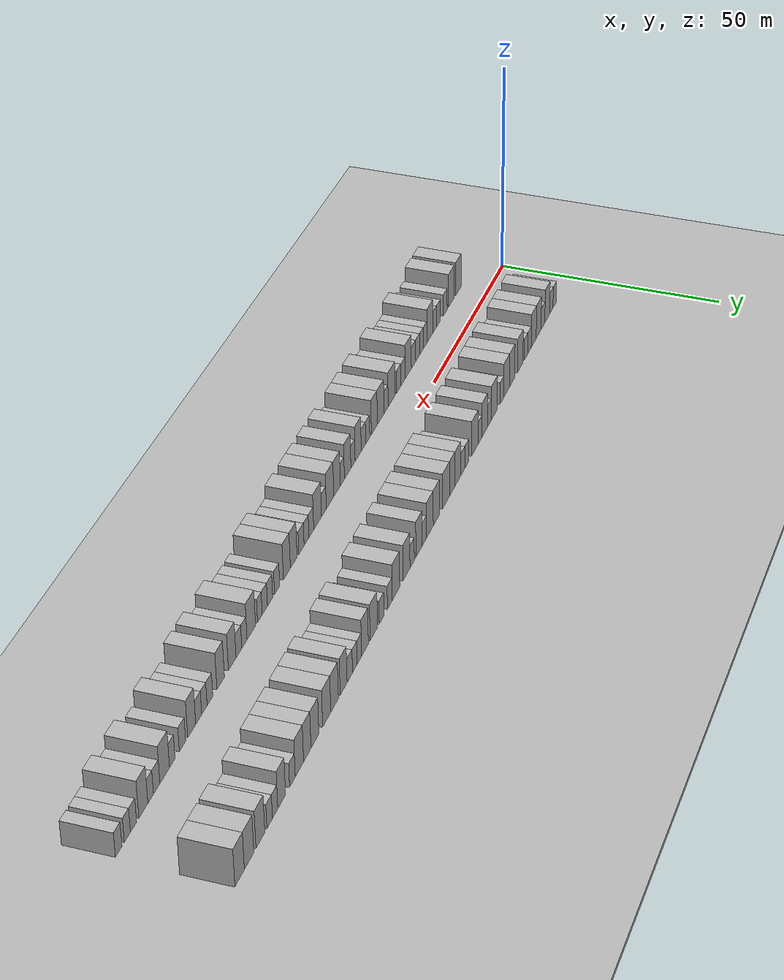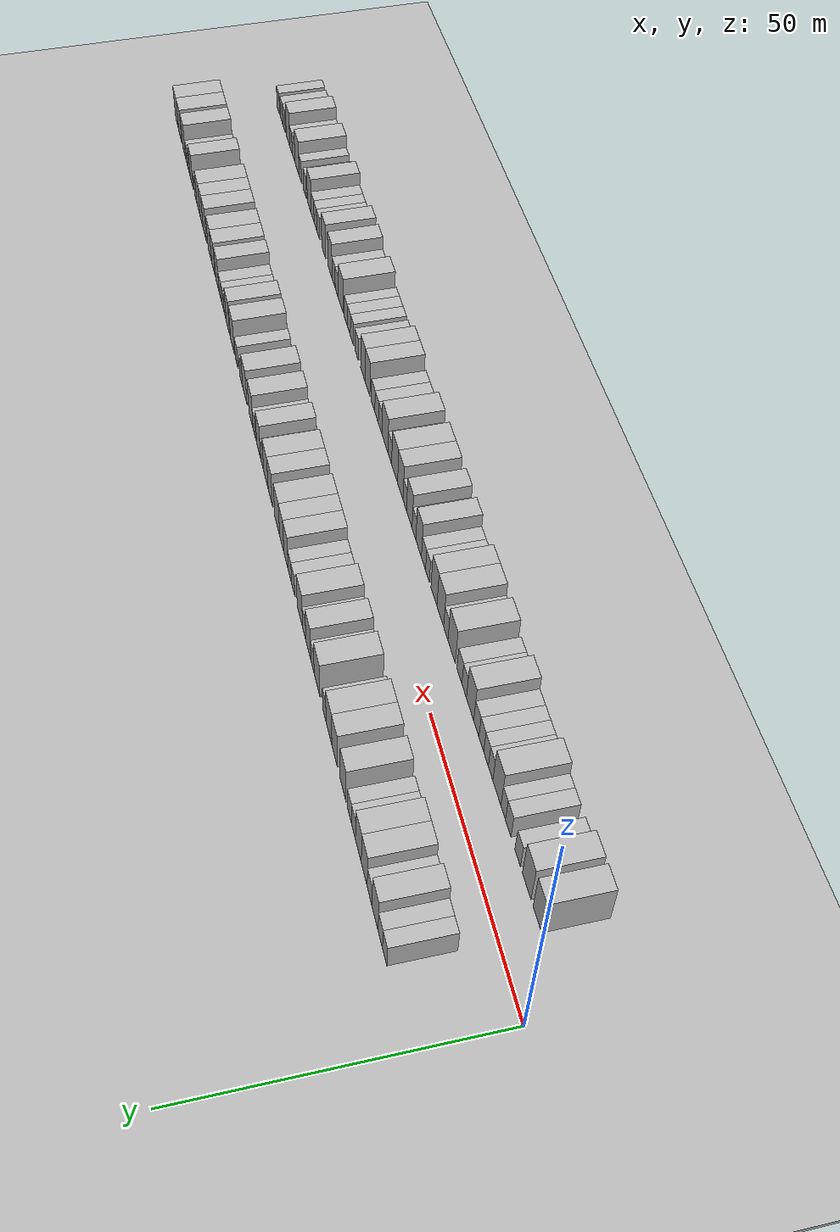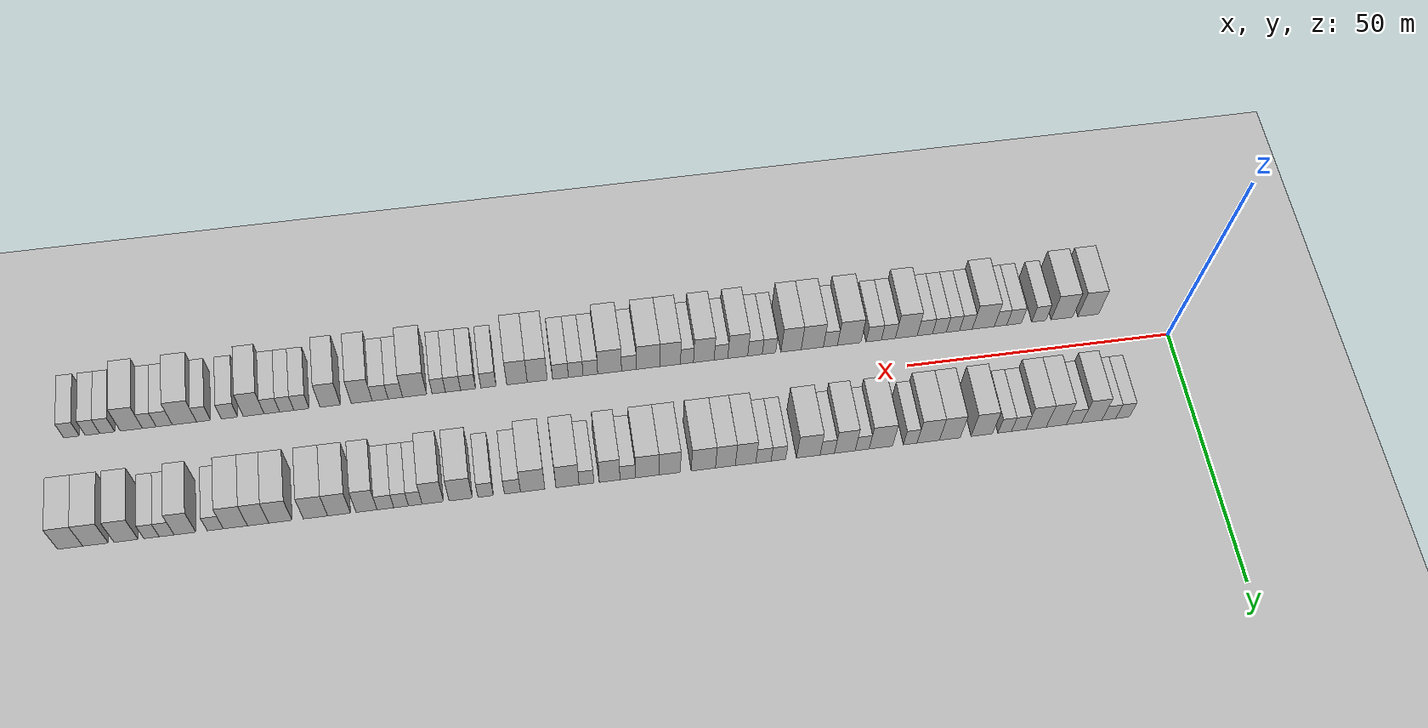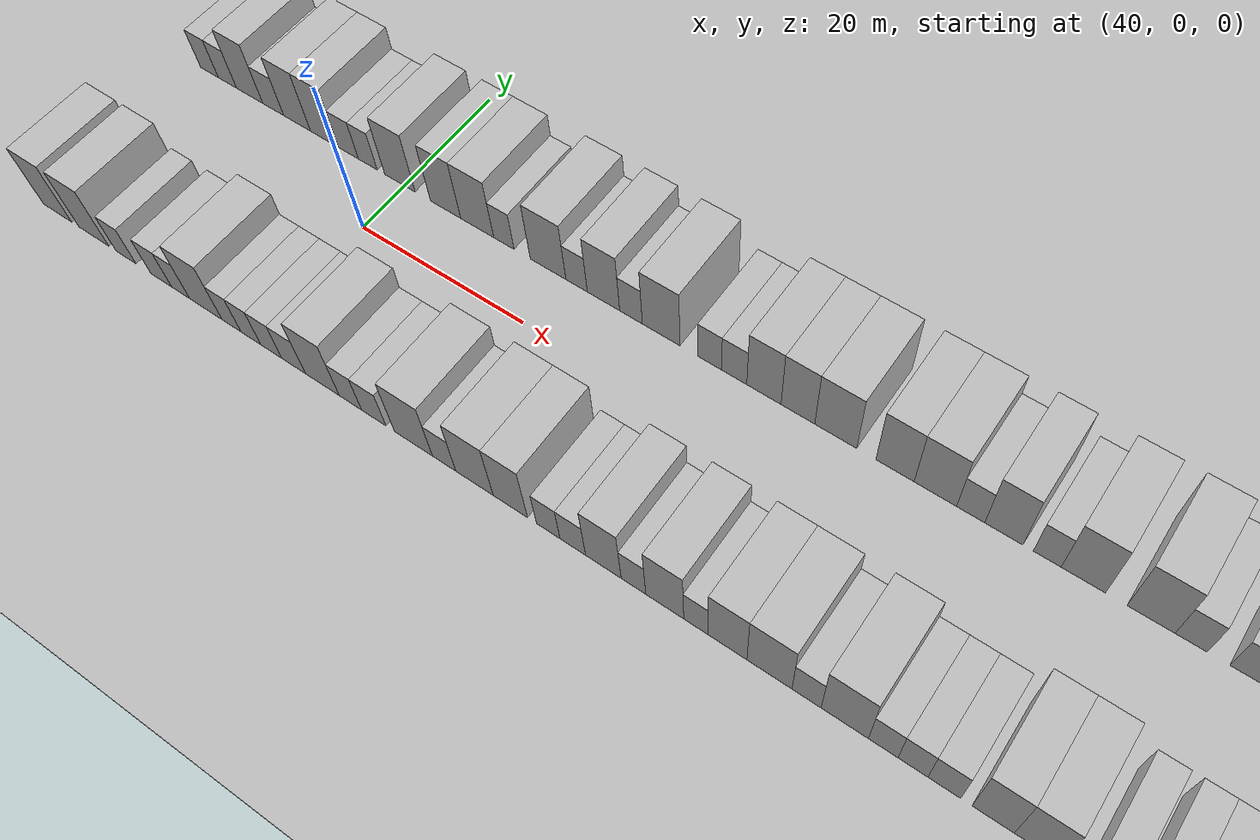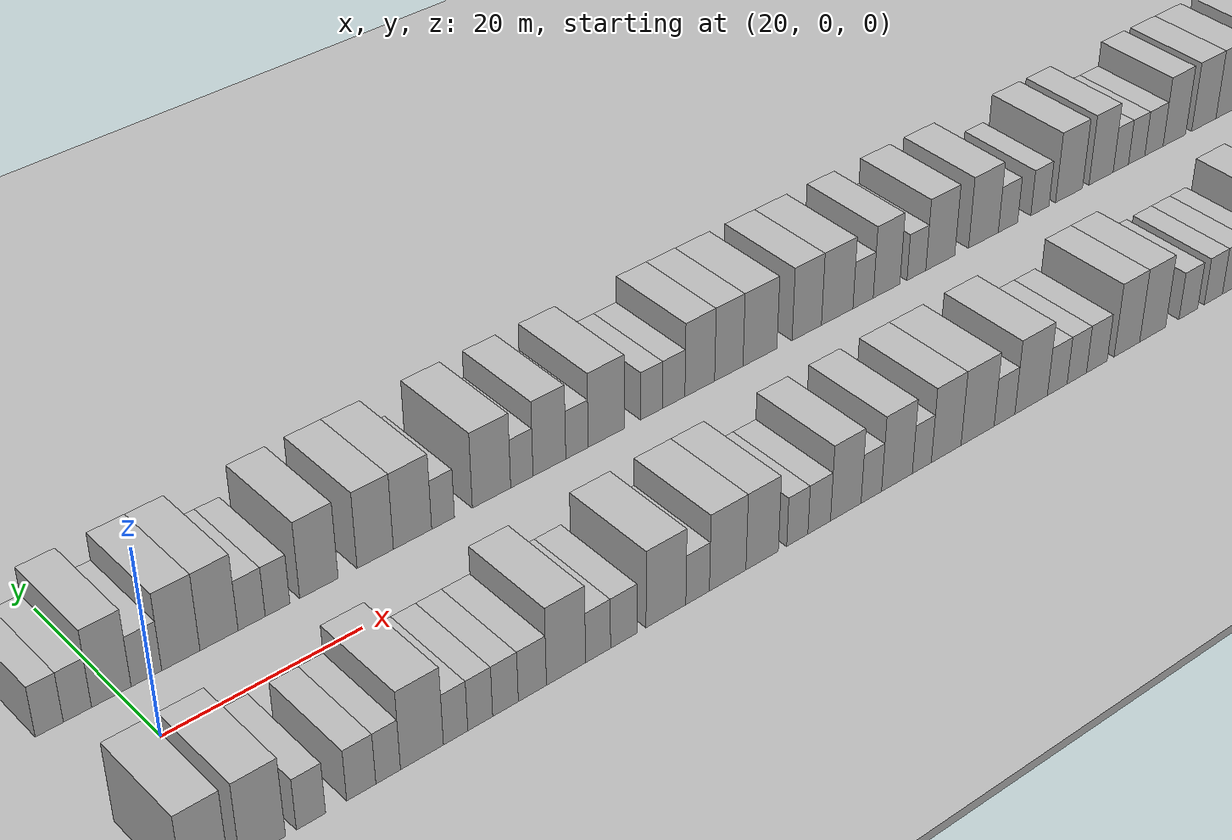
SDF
<?xml version="1.0" encoding="utf-8"?>

<sdf version="1.6">

   <world name="default">

      <gui fullscreen="0">

         <camera name="user_camera">

            <pose>-15 0 4.57585 0 0 0</pose>

            <view_controller>orbit</view_controller>

         </camera>

      </gui>

      <scene>

         <sky>

           <clouds>

             <speed>12</speed>

           </clouds>

         </sky>

         <ambient>0.4 0.4 0.4 1</ambient>

         <background>0.7 0.7 0.7 1</background>

         <shadows>1</shadows>

      </scene>

      <gravity>0 0 -9.8066</gravity>

      <magnetic_field>6e-06 2.3e-05 -4.2e-05</magnetic_field>

      <physics default="0" name="default_physics" type="ode">

         <ode>

            <solver>

               <type>quick</type>

               <iters>10</iters>

               <sor>1.0</sor>

               <use_dynamic_moi_rescaling>0</use_dynamic_moi_rescaling>

            </solver>

            <constraints>

               <cfm>0</cfm>

               <erp>0.2</erp>

               <contact_max_correcting_vel>100</contact_max_correcting_vel>

               <contact_surface_layer>0.001</contact_surface_layer>

            </constraints>

         </ode>

         <max_step_size>0.004</max_step_size>

         <real_time_factor>1</real_time_factor>

         <real_time_update_rate>250</real_time_update_rate>

      </physics>

      <light name="sun" type="directional">

         <cast_shadows>1</cast_shadows>

         <pose>0 0 10 0 0 0</pose>

         <diffuse>0.8 0.8 0.8 1</diffuse>

         <specular>0.2 0.2 0.2 1</specular>

         <attenuation>

            <range>1000</range>

            <constant>0.9</constant>

            <linear>0.01</linear>

            <quadratic>0.001</quadratic>

         </attenuation>

         <direction>-0.5 0.1 -0.9</direction>

      </light>

      <include>

         <name>ground_plane_1</name>

         <uri>model://HANNAS_ground_plane</uri>

         <pose>0 0 0  0 0 0</pose>

      </include>

      <include>

         <name>ground_plane_2</name>

         <uri>model://HANNAS_ground_plane</uri>

         <pose>100 0 0  0 0 0</pose>

      </include>

      <model name="building_1">

         <static>1</static>

         <pose frame="">13.2982 11.0000 0 0.000000 0.000000 1.570796</pose>

         <link name="link">

            <pose frame="">0 0 3.00 0 0 0</pose>

            <collision name="collision">

               <geometry>

                  <box>

                     <size>10.0000 2.5964 6.0000</size>

                  </box>

               </geometry>

               <max_contacts>10</max_contacts>

               <surface>

                  <contact>

                     <ode/>

                  </contact>

                  <bounce/>

                  <friction>

                     <torsional>

                        <ode/>

                     </torsional>

                     <ode/>

                  </friction>

               </surface>

            </collision>

            <visual name="visual">

               <cast_shadows>0</cast_shadows>

               <geometry>

                  <box>

                     <size>10.0000 2.5964 6.0000</size>

                  </box>

               </geometry>

               <material>

                  <script>

                     <uri>model://HANNAS_wall/materials/scripts</uri>

                     <uri>model://HANNAS_wall/materials/textures</uri>

                     <name>vrc/HANNAS_wall</name>

                  </script>

               </material>

            </visual>

            <self_collide>0</self_collide>

            <enable_wind>0</enable_wind>

            <kinematic>0</kinematic>

         </link>

      </model>

      <model name="building_2">

         <static>1</static>

         <pose frame="">15.9129 11.0000 0 0.000000 0.000000 1.570796</pose>

         <link name="link">

            <pose frame="">0 0 3.00 0 0 0</pose>

            <collision name="collision">

               <geometry>

                  <box>

                     <size>10.0000 2.6331 6.0000</size>

                  </box>

               </geometry>

               <max_contacts>10</max_contacts>

               <surface>

                  <contact>

                     <ode/>

                  </contact>

                  <bounce/>

                  <friction>

                     <torsional>

                        <ode/>

                     </torsional>

                     <ode/>

                  </friction>

               </surface>

            </collision>

            <visual name="visual">

               <cast_shadows>0</cast_shadows>

               <geometry>

                  <box>

                     <size>10.0000 2.6331 6.0000</size>

                  </box>

               </geometry>

               <material>

                  <script>

                     <uri>model://HANNAS_wall/materials/scripts</uri>

                     <uri>model://HANNAS_wall/materials/textures</uri>

                     <name>vrc/HANNAS_wall</name>

                  </script>

               </material>

            </visual>

            <self_collide>0</self_collide>

            <enable_wind>0</enable_wind>

            <kinematic>0</kinematic>

         </link>

      </model>

      <model name="building_3">

         <static>1</static>

         <pose frame="">19.1036 11.0000 0 0.000000 0.000000 1.570796</pose>

         <link name="link">

            <pose frame="">0 0 4.50 0 0 0</pose>

            <collision name="collision">

               <geometry>

                  <box>

                     <size>10.0000 3.7482 9.0000</size>

                  </box>

               </geometry>

               <max_contacts>10</max_contacts>

               <surface>

                  <contact>

                     <ode/>

                  </contact>

                  <bounce/>

                  <friction>

                     <torsional>

                        <ode/>

                     </torsional>

                     <ode/>

                  </friction>

               </surface>

            </collision>

            <visual name="visual">

               <cast_shadows>0</cast_shadows>

               <geometry>

                  <box>

                     <size>10.0000 3.7482 9.0000</size>

                  </box>

               </geometry>

               <material>

                  <script>

                     <uri>model://HANNAS_wall/materials/scripts</uri>

                     <uri>model://HANNAS_wall/materials/textures</uri>

                     <name>vrc/HANNAS_wall</name>

                  </script>

               </material>

            </visual>

            <self_collide>0</self_collide>

            <enable_wind>0</enable_wind>

            <kinematic>0</kinematic>

         </link>

      </model>

      <model name="building_4">

         <static>1</static>

         <pose frame="">22.4496 11.0000 0 0.000000 0.000000 1.570796</pose>

         <link name="link">

            <pose frame="">0 0 3.00 0 0 0</pose>

            <collision name="collision">

               <geometry>

                  <box>

                     <size>10.0000 2.9438 6.0000</size>

                  </box>

               </geometry>

               <max_contacts>10</max_contacts>

               <surface>

                  <contact>

                     <ode/>

                  </contact>

                  <bounce/>

                  <friction>

                     <torsional>

                        <ode/>

                     </torsional>

                     <ode/>

                  </friction>

               </surface>

            </collision>

            <visual name="visual">

               <cast_shadows>0</cast_shadows>

               <geometry>

                  <box>

                     <size>10.0000 2.9438 6.0000</size>

                  </box>

               </geometry>

               <material>

                  <script>

                     <uri>model://HANNAS_wall/materials/scripts</uri>

                     <uri>model://HANNAS_wall/materials/textures</uri>

                     <name>vrc/HANNAS_wall</name>

                  </script>

               </material>

            </visual>

            <self_collide>0</self_collide>

            <enable_wind>0</enable_wind>

            <kinematic>0</kinematic>

         </link>

      </model>

      <model name="building_5">

         <static>1</static>

         <pose frame="">25.7871 11.0000 0 0.000000 0.000000 1.570796</pose>

         <link name="link">

            <pose frame="">0 0 4.50 0 0 0</pose>

            <collision name="collision">

               <geometry>

                  <box>

                     <size>10.0000 3.7313 9.0000</size>

                  </box>

               </geometry>

               <max_contacts>10</max_contacts>

               <surface>

                  <contact>

                     <ode/>

                  </contact>

                  <bounce/>

                  <friction>

                     <torsional>

                        <ode/>

                     </torsional>

                     <ode/>

                  </friction>

               </surface>

            </collision>

            <visual name="visual">

               <cast_shadows>0</cast_shadows>

               <geometry>

                  <box>

                     <size>10.0000 3.7313 9.0000</size>

                  </box>

               </geometry>

               <material>

                  <script>

                     <uri>model://HANNAS_wall/materials/scripts</uri>

                     <uri>model://HANNAS_wall/materials/textures</uri>

                     <name>vrc/HANNAS_wall</name>

                  </script>

               </material>

            </visual>

            <self_collide>0</self_collide>

            <enable_wind>0</enable_wind>

            <kinematic>0</kinematic>

         </link>

      </model>

      <model name="building_6">

         <static>1</static>

         <pose frame="">29.5493 11.0000 0 0.000000 0.000000 1.570796</pose>

         <link name="link">

            <pose frame="">0 0 4.50 0 0 0</pose>

            <collision name="collision">

               <geometry>

                  <box>

                     <size>10.0000 3.7931 9.0000</size>

                  </box>

               </geometry>

               <max_contacts>10</max_contacts>

               <surface>

                  <contact>

                     <ode/>

                  </contact>

                  <bounce/>

                  <friction>

                     <torsional>

                        <ode/>

                     </torsional>

                     <ode/>

                  </friction>

               </surface>

            </collision>

            <visual name="visual">

               <cast_shadows>0</cast_shadows>

               <geometry>

                  <box>

                     <size>10.0000 3.7931 9.0000</size>

                  </box>

               </geometry>

               <material>

                  <script>

                     <uri>model://HANNAS_wall/materials/scripts</uri>

                     <uri>model://HANNAS_wall/materials/textures</uri>

                     <name>vrc/HANNAS_wall</name>

                  </script>

               </material>

            </visual>

            <self_collide>0</self_collide>

            <enable_wind>0</enable_wind>

            <kinematic>0</kinematic>

         </link>

      </model>

      <model name="building_7">

         <static>1</static>

         <pose frame="">32.8133 11.0000 0 0.000000 0.000000 1.570796</pose>

         <link name="link">

            <pose frame="">0 0 3.00 0 0 0</pose>

            <collision name="collision">

               <geometry>

                  <box>

                     <size>10.0000 2.7348 6.0000</size>

                  </box>

               </geometry>

               <max_contacts>10</max_contacts>

               <surface>

                  <contact>

                     <ode/>

                  </contact>

                  <bounce/>

                  <friction>

                     <torsional>

                        <ode/>

                     </torsional>

                     <ode/>

                  </friction>

               </surface>

            </collision>

            <visual name="visual">

               <cast_shadows>0</cast_shadows>

               <geometry>

                  <box>

                     <size>10.0000 2.7348 6.0000</size>

                  </box>

               </geometry>

               <material>

                  <script>

                     <uri>model://HANNAS_wall/materials/scripts</uri>

                     <uri>model://HANNAS_wall/materials/textures</uri>

                     <name>vrc/HANNAS_wall</name>

                  </script>

               </material>

            </visual>

            <self_collide>0</self_collide>

            <enable_wind>0</enable_wind>

            <kinematic>0</kinematic>

         </link>

      </model>

      <model name="building_8">

         <static>1</static>

         <pose frame="">35.4457 11.0000 0 0.000000 0.000000 1.570796</pose>

         <link name="link">

            <pose frame="">0 0 3.00 0 0 0</pose>

            <collision name="collision">

               <geometry>

                  <box>

                     <size>10.0000 2.5301 6.0000</size>

                  </box>

               </geometry>

               <max_contacts>10</max_contacts>

               <surface>

                  <contact>

                     <ode/>

                  </contact>

                  <bounce/>

                  <friction>

                     <torsional>

                        <ode/>

                     </torsional>

                     <ode/>

                  </friction>

               </surface>

            </collision>

            <visual name="visual">

               <cast_shadows>0</cast_shadows>

               <geometry>

                  <box>

                     <size>10.0000 2.5301 6.0000</size>

                  </box>

               </geometry>

               <material>

                  <script>

                     <uri>model://HANNAS_wall/materials/scripts</uri>

                     <uri>model://HANNAS_wall/materials/textures</uri>

                     <name>vrc/HANNAS_wall</name>

                  </script>

               </material>

            </visual>

            <self_collide>0</self_collide>

            <enable_wind>0</enable_wind>

            <kinematic>0</kinematic>

         </link>

      </model>

      <model name="building_9">

         <static>1</static>

         <pose frame="">39.7168 11.0000 0 0.000000 0.000000 1.570796</pose>

         <link name="link">

            <pose frame="">0 0 4.50 0 0 0</pose>

            <collision name="collision">

               <geometry>

                  <box>

                     <size>10.0000 4.0119 9.0000</size>

                  </box>

               </geometry>

               <max_contacts>10</max_contacts>

               <surface>

                  <contact>

                     <ode/>

                  </contact>

                  <bounce/>

                  <friction>

                     <torsional>

                        <ode/>

                     </torsional>

                     <ode/>

                  </friction>

               </surface>

            </collision>

            <visual name="visual">

               <cast_shadows>0</cast_shadows>

               <geometry>

                  <box>

                     <size>10.0000 4.0119 9.0000</size>

                  </box>

               </geometry>

               <material>

                  <script>

                     <uri>model://HANNAS_wall/materials/scripts</uri>

                     <uri>model://HANNAS_wall/materials/textures</uri>

                     <name>vrc/HANNAS_wall</name>

                  </script>

               </material>

            </visual>

            <self_collide>0</self_collide>

            <enable_wind>0</enable_wind>

            <kinematic>0</kinematic>

         </link>

      </model>

      <model name="building_10">

         <static>1</static>

         <pose frame="">45.6708 11.0000 0 0.000000 0.000000 1.570796</pose>

         <link name="link">

            <pose frame="">0 0 4.50 0 0 0</pose>

            <collision name="collision">

               <geometry>

                  <box>

                     <size>10.0000 3.8962 9.0000</size>

                  </box>

               </geometry>

               <max_contacts>10</max_contacts>

               <surface>

                  <contact>

                     <ode/>

                  </contact>

                  <bounce/>

                  <friction>

                     <torsional>

                        <ode/>

                     </torsional>

                     <ode/>

                  </friction>

               </surface>

            </collision>

            <visual name="visual">

               <cast_shadows>0</cast_shadows>

               <geometry>

                  <box>

                     <size>10.0000 3.8962 9.0000</size>

                  </box>

               </geometry>

               <material>

                  <script>

                     <uri>model://HANNAS_wall/materials/scripts</uri>

                     <uri>model://HANNAS_wall/materials/textures</uri>

                     <name>vrc/HANNAS_wall</name>

                  </script>

               </material>

            </visual>

            <self_collide>0</self_collide>

            <enable_wind>0</enable_wind>

            <kinematic>0</kinematic>

         </link>

      </model>

      <model name="building_11">

         <static>1</static>

         <pose frame="">49.7050 11.0000 0 0.000000 0.000000 1.570796</pose>

         <link name="link">

            <pose frame="">0 0 4.50 0 0 0</pose>

            <collision name="collision">

               <geometry>

                  <box>

                     <size>10.0000 4.1721 9.0000</size>

                  </box>

               </geometry>

               <max_contacts>10</max_contacts>

               <surface>

                  <contact>

                     <ode/>

                  </contact>

                  <bounce/>

                  <friction>

                     <torsional>

                        <ode/>

                     </torsional>

                     <ode/>

                  </friction>

               </surface>

            </collision>

            <visual name="visual">

               <cast_shadows>0</cast_shadows>

               <geometry>

                  <box>

                     <size>10.0000 4.1721 9.0000</size>

                  </box>

               </geometry>

               <material>

                  <script>

                     <uri>model://HANNAS_wall/materials/scripts</uri>

                     <uri>model://HANNAS_wall/materials/textures</uri>

                     <name>vrc/HANNAS_wall</name>

                  </script>

               </material>

            </visual>

            <self_collide>0</self_collide>

            <enable_wind>0</enable_wind>

            <kinematic>0</kinematic>

         </link>

      </model>

      <model name="building_12">

         <static>1</static>

         <pose frame="">53.0540 11.0000 0 0.000000 0.000000 1.570796</pose>

         <link name="link">

            <pose frame="">0 0 3.00 0 0 0</pose>

            <collision name="collision">

               <geometry>

                  <box>

                     <size>10.0000 2.5259 6.0000</size>

                  </box>

               </geometry>

               <max_contacts>10</max_contacts>

               <surface>

                  <contact>

                     <ode/>

                  </contact>

                  <bounce/>

                  <friction>

                     <torsional>

                        <ode/>

                     </torsional>

                     <ode/>

                  </friction>

               </surface>

            </collision>

            <visual name="visual">

               <cast_shadows>0</cast_shadows>

               <geometry>

                  <box>

                     <size>10.0000 2.5259 6.0000</size>

                  </box>

               </geometry>

               <material>

                  <script>

                     <uri>model://HANNAS_wall/materials/scripts</uri>

                     <uri>model://HANNAS_wall/materials/textures</uri>

                     <name>vrc/HANNAS_wall</name>

                  </script>

               </material>

            </visual>

            <self_collide>0</self_collide>

            <enable_wind>0</enable_wind>

            <kinematic>0</kinematic>

         </link>

      </model>

      <model name="building_13">

         <static>1</static>

         <pose frame="">58.4918 11.0000 0 0.000000 0.000000 1.570796</pose>

         <link name="link">

            <pose frame="">0 0 4.50 0 0 0</pose>

            <collision name="collision">

               <geometry>

                  <box>

                     <size>10.0000 4.3497 9.0000</size>

                  </box>

               </geometry>

               <max_contacts>10</max_contacts>

               <surface>

                  <contact>

                     <ode/>

                  </contact>

                  <bounce/>

                  <friction>

                     <torsional>

                        <ode/>

                     </torsional>

                     <ode/>

                  </friction>

               </surface>

            </collision>

            <visual name="visual">

               <cast_shadows>0</cast_shadows>

               <geometry>

                  <box>

                     <size>10.0000 4.3497 9.0000</size>

                  </box>

               </geometry>

               <material>

                  <script>

                     <uri>model://HANNAS_wall/materials/scripts</uri>

                     <uri>model://HANNAS_wall/materials/textures</uri>

                     <name>vrc/HANNAS_wall</name>

                  </script>

               </material>

            </visual>

            <self_collide>0</self_collide>

            <enable_wind>0</enable_wind>

            <kinematic>0</kinematic>

         </link>

      </model>

      <model name="building_14">

         <static>1</static>

         <pose frame="">61.9541 11.0000 0 0.000000 0.000000 1.570796</pose>

         <link name="link">

            <pose frame="">0 0 3.00 0 0 0</pose>

            <collision name="collision">

               <geometry>

                  <box>

                     <size>10.0000 2.5749 6.0000</size>

                  </box>

               </geometry>

               <max_contacts>10</max_contacts>

               <surface>

                  <contact>

                     <ode/>

                  </contact>

                  <bounce/>

                  <friction>

                     <torsional>

                        <ode/>

                     </torsional>

                     <ode/>

                  </friction>

               </surface>

            </collision>

            <visual name="visual">

               <cast_shadows>0</cast_shadows>

               <geometry>

                  <box>

                     <size>10.0000 2.5749 6.0000</size>

                  </box>

               </geometry>

               <material>

                  <script>

                     <uri>model://HANNAS_wall/materials/scripts</uri>

                     <uri>model://HANNAS_wall/materials/textures</uri>

                     <name>vrc/HANNAS_wall</name>

                  </script>

               </material>

            </visual>

            <self_collide>0</self_collide>

            <enable_wind>0</enable_wind>

            <kinematic>0</kinematic>

         </link>

      </model>

      <model name="building_15">

         <static>1</static>

         <pose frame="">65.1549 11.0000 0 0.000000 0.000000 1.570796</pose>

         <link name="link">

            <pose frame="">0 0 4.50 0 0 0</pose>

            <collision name="collision">

               <geometry>

                  <box>

                     <size>10.0000 3.8267 9.0000</size>

                  </box>

               </geometry>

               <max_contacts>10</max_contacts>

               <surface>

                  <contact>

                     <ode/>

                  </contact>

                  <bounce/>

                  <friction>

                     <torsional>

                        <ode/>

                     </torsional>

                     <ode/>

                  </friction>

               </surface>

            </collision>

            <visual name="visual">

               <cast_shadows>0</cast_shadows>

               <geometry>

                  <box>

                     <size>10.0000 3.8267 9.0000</size>

                  </box>

               </geometry>

               <material>

                  <script>

                     <uri>model://HANNAS_wall/materials/scripts</uri>

                     <uri>model://HANNAS_wall/materials/textures</uri>

                     <name>vrc/HANNAS_wall</name>

                  </script>

               </material>

            </visual>

            <self_collide>0</self_collide>

            <enable_wind>0</enable_wind>

            <kinematic>0</kinematic>

         </link>

      </model>

      <model name="building_16">

         <static>1</static>

         <pose frame="">68.3939 11.0000 0 0.000000 0.000000 1.570796</pose>

         <link name="link">

            <pose frame="">0 0 3.00 0 0 0</pose>

            <collision name="collision">

               <geometry>

                  <box>

                     <size>10.0000 2.6512 6.0000</size>

                  </box>

               </geometry>

               <max_contacts>10</max_contacts>

               <surface>

                  <contact>

                     <ode/>

                  </contact>

                  <bounce/>

                  <friction>

                     <torsional>

                        <ode/>

                     </torsional>

                     <ode/>

                  </friction>

               </surface>

            </collision>

            <visual name="visual">

               <cast_shadows>0</cast_shadows>

               <geometry>

                  <box>

                     <size>10.0000 2.6512 6.0000</size>

                  </box>

               </geometry>

               <material>

                  <script>

                     <uri>model://HANNAS_wall/materials/scripts</uri>

                     <uri>model://HANNAS_wall/materials/textures</uri>

                     <name>vrc/HANNAS_wall</name>

                  </script>

               </material>

            </visual>

            <self_collide>0</self_collide>

            <enable_wind>0</enable_wind>

            <kinematic>0</kinematic>

         </link>

      </model>

      <model name="building_17">

         <static>1</static>

         <pose frame="">71.8897 11.0000 0 0.000000 0.000000 1.570796</pose>

         <link name="link">

            <pose frame="">0 0 4.50 0 0 0</pose>

            <collision name="collision">

               <geometry>

                  <box>

                     <size>10.0000 4.3404 9.0000</size>

                  </box>

               </geometry>

               <max_contacts>10</max_contacts>

               <surface>

                  <contact>

                     <ode/>

                  </contact>

                  <bounce/>

                  <friction>

                     <torsional>

                        <ode/>

                     </torsional>

                     <ode/>

                  </friction>

               </surface>

            </collision>

            <visual name="visual">

               <cast_shadows>0</cast_shadows>

               <geometry>

                  <box>

                     <size>10.0000 4.3404 9.0000</size>

                  </box>

               </geometry>

               <material>

                  <script>

                     <uri>model://HANNAS_wall/materials/scripts</uri>

                     <uri>model://HANNAS_wall/materials/textures</uri>

                     <name>vrc/HANNAS_wall</name>

                  </script>

               </material>

            </visual>

            <self_collide>0</self_collide>

            <enable_wind>0</enable_wind>

            <kinematic>0</kinematic>

         </link>

      </model>

      <model name="building_18">

         <static>1</static>

         <pose frame="">77.3994 11.0000 0 0.000000 0.000000 1.570796</pose>

         <link name="link">

            <pose frame="">0 0 3.00 0 0 0</pose>

            <collision name="collision">

               <geometry>

                  <box>

                     <size>10.0000 2.6791 6.0000</size>

                  </box>

               </geometry>

               <max_contacts>10</max_contacts>

               <surface>

                  <contact>

                     <ode/>

                  </contact>

                  <bounce/>

                  <friction>

                     <torsional>

                        <ode/>

                     </torsional>

                     <ode/>

                  </friction>

               </surface>

            </collision>

            <visual name="visual">

               <cast_shadows>0</cast_shadows>

               <geometry>

                  <box>

                     <size>10.0000 2.6791 6.0000</size>

                  </box>

               </geometry>

               <material>

                  <script>

                     <uri>model://HANNAS_wall/materials/scripts</uri>

                     <uri>model://HANNAS_wall/materials/textures</uri>

                     <name>vrc/HANNAS_wall</name>

                  </script>

               </material>

            </visual>

            <self_collide>0</self_collide>

            <enable_wind>0</enable_wind>

            <kinematic>0</kinematic>

         </link>

      </model>

      <model name="building_19">

         <static>1</static>

         <pose frame="">80.1359 11.0000 0 0.000000 0.000000 1.570796</pose>

         <link name="link">

            <pose frame="">0 0 3.00 0 0 0</pose>

            <collision name="collision">

               <geometry>

                  <box>

                     <size>10.0000 2.7939 6.0000</size>

                  </box>

               </geometry>

               <max_contacts>10</max_contacts>

               <surface>

                  <contact>

                     <ode/>

                  </contact>

                  <bounce/>

                  <friction>

                     <torsional>

                        <ode/>

                     </torsional>

                     <ode/>

                  </friction>

               </surface>

            </collision>

            <visual name="visual">

               <cast_shadows>0</cast_shadows>

               <geometry>

                  <box>

                     <size>10.0000 2.7939 6.0000</size>

                  </box>

               </geometry>

               <material>

                  <script>

                     <uri>model://HANNAS_wall/materials/scripts</uri>

                     <uri>model://HANNAS_wall/materials/textures</uri>

                     <name>vrc/HANNAS_wall</name>

                  </script>

               </material>

            </visual>

            <self_collide>0</self_collide>

            <enable_wind>0</enable_wind>

            <kinematic>0</kinematic>

         </link>

      </model>

      <model name="building_20">

         <static>1</static>

         <pose frame="">83.4077 11.0000 0 0.000000 0.000000 1.570796</pose>

         <link name="link">

            <pose frame="">0 0 4.50 0 0 0</pose>

            <collision name="collision">

               <geometry>

                  <box>

                     <size>10.0000 3.7497 9.0000</size>

                  </box>

               </geometry>

               <max_contacts>10</max_contacts>

               <surface>

                  <contact>

                     <ode/>

                  </contact>

                  <bounce/>

                  <friction>

                     <torsional>

                        <ode/>

                     </torsional>

                     <ode/>

                  </friction>

               </surface>

            </collision>

            <visual name="visual">

               <cast_shadows>0</cast_shadows>

               <geometry>

                  <box>

                     <size>10.0000 3.7497 9.0000</size>

                  </box>

               </geometry>

               <material>

                  <script>

                     <uri>model://HANNAS_wall/materials/scripts</uri>

                     <uri>model://HANNAS_wall/materials/textures</uri>

                     <name>vrc/HANNAS_wall</name>

                  </script>

               </material>

            </visual>

            <self_collide>0</self_collide>

            <enable_wind>0</enable_wind>

            <kinematic>0</kinematic>

         </link>

      </model>

      <model name="building_21">

         <static>1</static>

         <pose frame="">87.1007 11.0000 0 0.000000 0.000000 1.570796</pose>

         <link name="link">

            <pose frame="">0 0 4.50 0 0 0</pose>

            <collision name="collision">

               <geometry>

                  <box>

                     <size>10.0000 3.6362 9.0000</size>

                  </box>

               </geometry>

               <max_contacts>10</max_contacts>

               <surface>

                  <contact>

                     <ode/>

                  </contact>

                  <bounce/>

                  <friction>

                     <torsional>

                        <ode/>

                     </torsional>

                     <ode/>

                  </friction>

               </surface>

            </collision>

            <visual name="visual">

               <cast_shadows>0</cast_shadows>

               <geometry>

                  <box>

                     <size>10.0000 3.6362 9.0000</size>

                  </box>

               </geometry>

               <material>

                  <script>

                     <uri>model://HANNAS_wall/materials/scripts</uri>

                     <uri>model://HANNAS_wall/materials/textures</uri>

                     <name>vrc/HANNAS_wall</name>

                  </script>

               </material>

            </visual>

            <self_collide>0</self_collide>

            <enable_wind>0</enable_wind>

            <kinematic>0</kinematic>

         </link>

      </model>

      <model name="building_22">

         <static>1</static>

         <pose frame="">91.1329 11.0000 0 0.000000 0.000000 1.570796</pose>

         <link name="link">

            <pose frame="">0 0 4.50 0 0 0</pose>

            <collision name="collision">

               <geometry>

                  <box>

                     <size>10.0000 4.4283 9.0000</size>

                  </box>

               </geometry>

               <max_contacts>10</max_contacts>

               <surface>

                  <contact>

                     <ode/>

                  </contact>

                  <bounce/>

                  <friction>

                     <torsional>

                        <ode/>

                     </torsional>

                     <ode/>

                  </friction>

               </surface>

            </collision>

            <visual name="visual">

               <cast_shadows>0</cast_shadows>

               <geometry>

                  <box>

                     <size>10.0000 4.4283 9.0000</size>

                  </box>

               </geometry>

               <material>

                  <script>

                     <uri>model://HANNAS_wall/materials/scripts</uri>

                     <uri>model://HANNAS_wall/materials/textures</uri>

                     <name>vrc/HANNAS_wall</name>

                  </script>

               </material>

            </visual>

            <self_collide>0</self_collide>

            <enable_wind>0</enable_wind>

            <kinematic>0</kinematic>

         </link>

      </model>

      <model name="building_23">

         <static>1</static>

         <pose frame="">97.3107 11.0000 0 0.000000 0.000000 1.570796</pose>

         <link name="link">

            <pose frame="">0 0 4.50 0 0 0</pose>

            <collision name="collision">

               <geometry>

                  <box>

                     <size>10.0000 3.9274 9.0000</size>

                  </box>

               </geometry>

               <max_contacts>10</max_contacts>

               <surface>

                  <contact>

                     <ode/>

                  </contact>

                  <bounce/>

                  <friction>

                     <torsional>

                        <ode/>

                     </torsional>

                     <ode/>

                  </friction>

               </surface>

            </collision>

            <visual name="visual">

               <cast_shadows>0</cast_shadows>

               <geometry>

                  <box>

                     <size>10.0000 3.9274 9.0000</size>

                  </box>

               </geometry>

               <material>

                  <script>

                     <uri>model://HANNAS_wall/materials/scripts</uri>

                     <uri>model://HANNAS_wall/materials/textures</uri>

                     <name>vrc/HANNAS_wall</name>

                  </script>

               </material>

            </visual>

            <self_collide>0</self_collide>

            <enable_wind>0</enable_wind>

            <kinematic>0</kinematic>

         </link>

      </model>

      <model name="building_24">

         <static>1</static>

         <pose frame="">101.4170 11.0000 0 0.000000 0.000000 1.570796</pose>

         <link name="link">

            <pose frame="">0 0 4.50 0 0 0</pose>

            <collision name="collision">

               <geometry>

                  <box>

                     <size>10.0000 4.2852 9.0000</size>

                  </box>

               </geometry>

               <max_contacts>10</max_contacts>

               <surface>

                  <contact>

                     <ode/>

                  </contact>

                  <bounce/>

                  <friction>

                     <torsional>

                        <ode/>

                     </torsional>

                     <ode/>

                  </friction>

               </surface>

            </collision>

            <visual name="visual">

               <cast_shadows>0</cast_shadows>

               <geometry>

                  <box>

                     <size>10.0000 4.2852 9.0000</size>

                  </box>

               </geometry>

               <material>

                  <script>

                     <uri>model://HANNAS_wall/materials/scripts</uri>

                     <uri>model://HANNAS_wall/materials/textures</uri>

                     <name>vrc/HANNAS_wall</name>

                  </script>

               </material>

            </visual>

            <self_collide>0</self_collide>

            <enable_wind>0</enable_wind>

            <kinematic>0</kinematic>

         </link>

      </model>

      <model name="building_25">

         <static>1</static>

         <pose frame="">104.9561 11.0000 0 0.000000 0.000000 1.570796</pose>

         <link name="link">

            <pose frame="">0 0 3.00 0 0 0</pose>

            <collision name="collision">

               <geometry>

                  <box>

                     <size>10.0000 2.7929 6.0000</size>

                  </box>

               </geometry>

               <max_contacts>10</max_contacts>

               <surface>

                  <contact>

                     <ode/>

                  </contact>

                  <bounce/>

                  <friction>

                     <torsional>

                        <ode/>

                     </torsional>

                     <ode/>

                  </friction>

               </surface>

            </collision>

            <visual name="visual">

               <cast_shadows>0</cast_shadows>

               <geometry>

                  <box>

                     <size>10.0000 2.7929 6.0000</size>

                  </box>

               </geometry>

               <material>

                  <script>

                     <uri>model://HANNAS_wall/materials/scripts</uri>

                     <uri>model://HANNAS_wall/materials/textures</uri>

                     <name>vrc/HANNAS_wall</name>

                  </script>

               </material>

            </visual>

            <self_collide>0</self_collide>

            <enable_wind>0</enable_wind>

            <kinematic>0</kinematic>

         </link>

      </model>

      <model name="building_26">

         <static>1</static>

         <pose frame="">108.2186 11.0000 0 0.000000 0.000000 1.570796</pose>

         <link name="link">

            <pose frame="">0 0 4.50 0 0 0</pose>

            <collision name="collision">

               <geometry>

                  <box>

                     <size>10.0000 3.7321 9.0000</size>

                  </box>

               </geometry>

               <max_contacts>10</max_contacts>

               <surface>

                  <contact>

                     <ode/>

                  </contact>

                  <bounce/>

                  <friction>

                     <torsional>

                        <ode/>

                     </torsional>

                     <ode/>

                  </friction>

               </surface>

            </collision>

            <visual name="visual">

               <cast_shadows>0</cast_shadows>

               <geometry>

                  <box>

                     <size>10.0000 3.7321 9.0000</size>

                  </box>

               </geometry>

               <material>

                  <script>

                     <uri>model://HANNAS_wall/materials/scripts</uri>

                     <uri>model://HANNAS_wall/materials/textures</uri>

                     <name>vrc/HANNAS_wall</name>

                  </script>

               </material>

            </visual>

            <self_collide>0</self_collide>

            <enable_wind>0</enable_wind>

            <kinematic>0</kinematic>

         </link>

      </model>

      <model name="building_27">

         <static>1</static>

         <pose frame="">112.4197 11.0000 0 0.000000 0.000000 1.570796</pose>

         <link name="link">

            <pose frame="">0 0 3.00 0 0 0</pose>

            <collision name="collision">

               <geometry>

                  <box>

                     <size>10.0000 2.6702 6.0000</size>

                  </box>

               </geometry>

               <max_contacts>10</max_contacts>

               <surface>

                  <contact>

                     <ode/>

                  </contact>

                  <bounce/>

                  <friction>

                     <torsional>

                        <ode/>

                     </torsional>

                     <ode/>

                  </friction>

               </surface>

            </collision>

            <visual name="visual">

               <cast_shadows>0</cast_shadows>

               <geometry>

                  <box>

                     <size>10.0000 2.6702 6.0000</size>

                  </box>

               </geometry>

               <material>

                  <script>

                     <uri>model://HANNAS_wall/materials/scripts</uri>

                     <uri>model://HANNAS_wall/materials/textures</uri>

                     <name>vrc/HANNAS_wall</name>

                  </script>

               </material>

            </visual>

            <self_collide>0</self_collide>

            <enable_wind>0</enable_wind>

            <kinematic>0</kinematic>

         </link>

      </model>

      <model name="building_28">

         <static>1</static>

         <pose frame="">115.8451 11.0000 0 0.000000 0.000000 1.570796</pose>

         <link name="link">

            <pose frame="">0 0 4.50 0 0 0</pose>

            <collision name="collision">

               <geometry>

                  <box>

                     <size>10.0000 4.1805 9.0000</size>

                  </box>

               </geometry>

               <max_contacts>10</max_contacts>

               <surface>

                  <contact>

                     <ode/>

                  </contact>

                  <bounce/>

                  <friction>

                     <torsional>

                        <ode/>

                     </torsional>

                     <ode/>

                  </friction>

               </surface>

            </collision>

            <visual name="visual">

               <cast_shadows>0</cast_shadows>

               <geometry>

                  <box>

                     <size>10.0000 4.1805 9.0000</size>

                  </box>

               </geometry>

               <material>

                  <script>

                     <uri>model://HANNAS_wall/materials/scripts</uri>

                     <uri>model://HANNAS_wall/materials/textures</uri>

                     <name>vrc/HANNAS_wall</name>

                  </script>

               </material>

            </visual>

            <self_collide>0</self_collide>

            <enable_wind>0</enable_wind>

            <kinematic>0</kinematic>

         </link>

      </model>

      <model name="building_29">

         <static>1</static>

         <pose frame="">122.1310 11.0000 0 0.000000 0.000000 1.570796</pose>

         <link name="link">

            <pose frame="">0 0 4.50 0 0 0</pose>

            <collision name="collision">

               <geometry>

                  <box>

                     <size>10.0000 4.3913 9.0000</size>

                  </box>

               </geometry>

               <max_contacts>10</max_contacts>

               <surface>

                  <contact>

                     <ode/>

                  </contact>

                  <bounce/>

                  <friction>

                     <torsional>

                        <ode/>

                     </torsional>

                     <ode/>

                  </friction>

               </surface>

            </collision>

            <visual name="visual">

               <cast_shadows>0</cast_shadows>

               <geometry>

                  <box>

                     <size>10.0000 4.3913 9.0000</size>

                  </box>

               </geometry>

               <material>

                  <script>

                     <uri>model://HANNAS_wall/materials/scripts</uri>

                     <uri>model://HANNAS_wall/materials/textures</uri>

                     <name>vrc/HANNAS_wall</name>

                  </script>

               </material>

            </visual>

            <self_collide>0</self_collide>

            <enable_wind>0</enable_wind>

            <kinematic>0</kinematic>

         </link>

      </model>

      <model name="building_30">

         <static>1</static>

         <pose frame="">125.7709 11.0000 0 0.000000 0.000000 1.570796</pose>

         <link name="link">

            <pose frame="">0 0 3.00 0 0 0</pose>

            <collision name="collision">

               <geometry>

                  <box>

                     <size>10.0000 2.8885 6.0000</size>

                  </box>

               </geometry>

               <max_contacts>10</max_contacts>

               <surface>

                  <contact>

                     <ode/>

                  </contact>

                  <bounce/>

                  <friction>

                     <torsional>

                        <ode/>

                     </torsional>

                     <ode/>

                  </friction>

               </surface>

            </collision>

            <visual name="visual">

               <cast_shadows>0</cast_shadows>

               <geometry>

                  <box>

                     <size>10.0000 2.8885 6.0000</size>

                  </box>

               </geometry>

               <material>

                  <script>

                     <uri>model://HANNAS_wall/materials/scripts</uri>

                     <uri>model://HANNAS_wall/materials/textures</uri>

                     <name>vrc/HANNAS_wall</name>

                  </script>

               </material>

            </visual>

            <self_collide>0</self_collide>

            <enable_wind>0</enable_wind>

            <kinematic>0</kinematic>

         </link>

      </model>

      <model name="building_31">

         <static>1</static>

         <pose frame="">130.5953 11.0000 0 0.000000 0.000000 1.570796</pose>

         <link name="link">

            <pose frame="">0 0 3.00 0 0 0</pose>

            <collision name="collision">

               <geometry>

                  <box>

                     <size>10.0000 2.7602 6.0000</size>

                  </box>

               </geometry>

               <max_contacts>10</max_contacts>

               <surface>

                  <contact>

                     <ode/>

                  </contact>

                  <bounce/>

                  <friction>

                     <torsional>

                        <ode/>

                     </torsional>

                     <ode/>

                  </friction>

               </surface>

            </collision>

            <visual name="visual">

               <cast_shadows>0</cast_shadows>

               <geometry>

                  <box>

                     <size>10.0000 2.7602 6.0000</size>

                  </box>

               </geometry>

               <material>

                  <script>

                     <uri>model://HANNAS_wall/materials/scripts</uri>

                     <uri>model://HANNAS_wall/materials/textures</uri>

                     <name>vrc/HANNAS_wall</name>

                  </script>

               </material>

            </visual>

            <self_collide>0</self_collide>

            <enable_wind>0</enable_wind>

            <kinematic>0</kinematic>

         </link>

      </model>

      <model name="building_32">

         <static>1</static>

         <pose frame="">135.0744 11.0000 0 0.000000 0.000000 1.570796</pose>

         <link name="link">

            <pose frame="">0 0 4.50 0 0 0</pose>

            <collision name="collision">

               <geometry>

                  <box>

                     <size>10.0000 4.1980 9.0000</size>

                  </box>

               </geometry>

               <max_contacts>10</max_contacts>

               <surface>

                  <contact>

                     <ode/>

                  </contact>

                  <bounce/>

                  <friction>

                     <torsional>

                        <ode/>

                     </torsional>

                     <ode/>

                  </friction>

               </surface>

            </collision>

            <visual name="visual">

               <cast_shadows>0</cast_shadows>

               <geometry>

                  <box>

                     <size>10.0000 4.1980 9.0000</size>

                  </box>

               </geometry>

               <material>

                  <script>

                     <uri>model://HANNAS_wall/materials/scripts</uri>

                     <uri>model://HANNAS_wall/materials/textures</uri>

                     <name>vrc/HANNAS_wall</name>

                  </script>

               </material>

            </visual>

            <self_collide>0</self_collide>

            <enable_wind>0</enable_wind>

            <kinematic>0</kinematic>

         </link>

      </model>

      <model name="building_33">

         <static>1</static>

         <pose frame="">140.0849 11.0000 0 0.000000 0.000000 1.570796</pose>

         <link name="link">

            <pose frame="">0 0 4.50 0 0 0</pose>

            <collision name="collision">

               <geometry>

                  <box>

                     <size>10.0000 3.8230 9.0000</size>

                  </box>

               </geometry>

               <max_contacts>10</max_contacts>

               <surface>

                  <contact>

                     <ode/>

                  </contact>

                  <bounce/>

                  <friction>

                     <torsional>

                        <ode/>

                     </torsional>

                     <ode/>

                  </friction>

               </surface>

            </collision>

            <visual name="visual">

               <cast_shadows>0</cast_shadows>

               <geometry>

                  <box>

                     <size>10.0000 3.8230 9.0000</size>

                  </box>

               </geometry>

               <material>

                  <script>

                     <uri>model://HANNAS_wall/materials/scripts</uri>

                     <uri>model://HANNAS_wall/materials/textures</uri>

                     <name>vrc/HANNAS_wall</name>

                  </script>

               </material>

            </visual>

            <self_collide>0</self_collide>

            <enable_wind>0</enable_wind>

            <kinematic>0</kinematic>

         </link>

      </model>

      <model name="building_34">

         <static>1</static>

         <pose frame="">143.2163 11.0000 0 0.000000 0.000000 1.570796</pose>

         <link name="link">

            <pose frame="">0 0 3.00 0 0 0</pose>

            <collision name="collision">

               <geometry>

                  <box>

                     <size>10.0000 2.4398 6.0000</size>

                  </box>

               </geometry>

               <max_contacts>10</max_contacts>

               <surface>

                  <contact>

                     <ode/>

                  </contact>

                  <bounce/>

                  <friction>

                     <torsional>

                        <ode/>

                     </torsional>

                     <ode/>

                  </friction>

               </surface>

            </collision>

            <visual name="visual">

               <cast_shadows>0</cast_shadows>

               <geometry>

                  <box>

                     <size>10.0000 2.4398 6.0000</size>

                  </box>

               </geometry>

               <material>

                  <script>

                     <uri>model://HANNAS_wall/materials/scripts</uri>

                     <uri>model://HANNAS_wall/materials/textures</uri>

                     <name>vrc/HANNAS_wall</name>

                  </script>

               </material>

            </visual>

            <self_collide>0</self_collide>

            <enable_wind>0</enable_wind>

            <kinematic>0</kinematic>

         </link>

      </model>

      <model name="building_35">

         <static>1</static>

         <pose frame="">145.7542 11.0000 0 0.000000 0.000000 1.570796</pose>

         <link name="link">

            <pose frame="">0 0 3.00 0 0 0</pose>

            <collision name="collision">

               <geometry>

                  <box>

                     <size>10.0000 2.6360 6.0000</size>

                  </box>

               </geometry>

               <max_contacts>10</max_contacts>

               <surface>

                  <contact>

                     <ode/>

                  </contact>

                  <bounce/>

                  <friction>

                     <torsional>

                        <ode/>

                     </torsional>

                     <ode/>

                  </friction>

               </surface>

            </collision>

            <visual name="visual">

               <cast_shadows>0</cast_shadows>

               <geometry>

                  <box>

                     <size>10.0000 2.6360 6.0000</size>

                  </box>

               </geometry>

               <material>

                  <script>

                     <uri>model://HANNAS_wall/materials/scripts</uri>

                     <uri>model://HANNAS_wall/materials/textures</uri>

                     <name>vrc/HANNAS_wall</name>

                  </script>

               </material>

            </visual>

            <self_collide>0</self_collide>

            <enable_wind>0</enable_wind>

            <kinematic>0</kinematic>

         </link>

      </model>

      <model name="building_36">

         <static>1</static>

         <pose frame="">148.5625 11.0000 0 0.000000 0.000000 1.570796</pose>

         <link name="link">

            <pose frame="">0 0 3.00 0 0 0</pose>

            <collision name="collision">

               <geometry>

                  <box>

                     <size>10.0000 2.9808 6.0000</size>

                  </box>

               </geometry>

               <max_contacts>10</max_contacts>

               <surface>

                  <contact>

                     <ode/>

                  </contact>

                  <bounce/>

                  <friction>

                     <torsional>

                        <ode/>

                     </torsional>

                     <ode/>

                  </friction>

               </surface>

            </collision>

            <visual name="visual">

               <cast_shadows>0</cast_shadows>

               <geometry>

                  <box>

                     <size>10.0000 2.9808 6.0000</size>

                  </box>

               </geometry>

               <material>

                  <script>

                     <uri>model://HANNAS_wall/materials/scripts</uri>

                     <uri>model://HANNAS_wall/materials/textures</uri>

                     <name>vrc/HANNAS_wall</name>

                  </script>

               </material>

            </visual>

            <self_collide>0</self_collide>

            <enable_wind>0</enable_wind>

            <kinematic>0</kinematic>

         </link>

      </model>

      <model name="building_37">

         <static>1</static>

         <pose frame="">151.9201 11.0000 0 0.000000 0.000000 1.570796</pose>

         <link name="link">

            <pose frame="">0 0 4.50 0 0 0</pose>

            <collision name="collision">

               <geometry>

                  <box>

                     <size>10.0000 3.7343 9.0000</size>

                  </box>

               </geometry>

               <max_contacts>10</max_contacts>

               <surface>

                  <contact>

                     <ode/>

                  </contact>

                  <bounce/>

                  <friction>

                     <torsional>

                        <ode/>

                     </torsional>

                     <ode/>

                  </friction>

               </surface>

            </collision>

            <visual name="visual">

               <cast_shadows>0</cast_shadows>

               <geometry>

                  <box>

                     <size>10.0000 3.7343 9.0000</size>

                  </box>

               </geometry>

               <material>

                  <script>

                     <uri>model://HANNAS_wall/materials/scripts</uri>

                     <uri>model://HANNAS_wall/materials/textures</uri>

                     <name>vrc/HANNAS_wall</name>

                  </script>

               </material>

            </visual>

            <self_collide>0</self_collide>

            <enable_wind>0</enable_wind>

            <kinematic>0</kinematic>

         </link>

      </model>

      <model name="building_38">

         <static>1</static>

         <pose frame="">156.8226 11.0000 0 0.000000 0.000000 1.570796</pose>

         <link name="link">

            <pose frame="">0 0 4.50 0 0 0</pose>

            <collision name="collision">

               <geometry>

                  <box>

                     <size>10.0000 4.0708 9.0000</size>

                  </box>

               </geometry>

               <max_contacts>10</max_contacts>

               <surface>

                  <contact>

                     <ode/>

                  </contact>

                  <bounce/>

                  <friction>

                     <torsional>

                        <ode/>

                     </torsional>

                     <ode/>

                  </friction>

               </surface>

            </collision>

            <visual name="visual">

               <cast_shadows>0</cast_shadows>

               <geometry>

                  <box>

                     <size>10.0000 4.0708 9.0000</size>

                  </box>

               </geometry>

               <material>

                  <script>

                     <uri>model://HANNAS_wall/materials/scripts</uri>

                     <uri>model://HANNAS_wall/materials/textures</uri>

                     <name>vrc/HANNAS_wall</name>

                  </script>

               </material>

            </visual>

            <self_collide>0</self_collide>

            <enable_wind>0</enable_wind>

            <kinematic>0</kinematic>

         </link>

      </model>

      <model name="building_39">

         <static>1</static>

         <pose frame="">161.0073 11.0000 0 0.000000 0.000000 1.570796</pose>

         <link name="link">

            <pose frame="">0 0 4.50 0 0 0</pose>

            <collision name="collision">

               <geometry>

                  <box>

                     <size>10.0000 4.2986 9.0000</size>

                  </box>

               </geometry>

               <max_contacts>10</max_contacts>

               <surface>

                  <contact>

                     <ode/>

                  </contact>

                  <bounce/>

                  <friction>

                     <torsional>

                        <ode/>

                     </torsional>

                     <ode/>

                  </friction>

               </surface>

            </collision>

            <visual name="visual">

               <cast_shadows>0</cast_shadows>

               <geometry>

                  <box>

                     <size>10.0000 4.2986 9.0000</size>

                  </box>

               </geometry>

               <material>

                  <script>

                     <uri>model://HANNAS_wall/materials/scripts</uri>

                     <uri>model://HANNAS_wall/materials/textures</uri>

                     <name>vrc/HANNAS_wall</name>

                  </script>

               </material>

            </visual>

            <self_collide>0</self_collide>

            <enable_wind>0</enable_wind>

            <kinematic>0</kinematic>

         </link>

      </model>

      <model name="building_40">

         <static>1</static>

         <pose frame="">167.2111 11.0000 0 0.000000 0.000000 1.570796</pose>

         <link name="link">

            <pose frame="">0 0 4.50 0 0 0</pose>

            <collision name="collision">

               <geometry>

                  <box>

                     <size>10.0000 4.1090 9.0000</size>

                  </box>

               </geometry>

               <max_contacts>10</max_contacts>

               <surface>

                  <contact>

                     <ode/>

                  </contact>

                  <bounce/>

                  <friction>

                     <torsional>

                        <ode/>

                     </torsional>

                     <ode/>

                  </friction>

               </surface>

            </collision>

            <visual name="visual">

               <cast_shadows>0</cast_shadows>

               <geometry>

                  <box>

                     <size>10.0000 4.1090 9.0000</size>

                  </box>

               </geometry>

               <material>

                  <script>

                     <uri>model://HANNAS_wall/materials/scripts</uri>

                     <uri>model://HANNAS_wall/materials/textures</uri>

                     <name>vrc/HANNAS_wall</name>

                  </script>

               </material>

            </visual>

            <self_collide>0</self_collide>

            <enable_wind>0</enable_wind>

            <kinematic>0</kinematic>

         </link>

      </model>

      <model name="building_41">

         <static>1</static>

         <pose frame="">171.1604 11.0000 0 0.000000 0.000000 1.570796</pose>

         <link name="link">

            <pose frame="">0 0 4.50 0 0 0</pose>

            <collision name="collision">

               <geometry>

                  <box>

                     <size>10.0000 3.7896 9.0000</size>

                  </box>

               </geometry>

               <max_contacts>10</max_contacts>

               <surface>

                  <contact>

                     <ode/>

                  </contact>

                  <bounce/>

                  <friction>

                     <torsional>

                        <ode/>

                     </torsional>

                     <ode/>

                  </friction>

               </surface>

            </collision>

            <visual name="visual">

               <cast_shadows>0</cast_shadows>

               <geometry>

                  <box>

                     <size>10.0000 3.7896 9.0000</size>

                  </box>

               </geometry>

               <material>

                  <script>

                     <uri>model://HANNAS_wall/materials/scripts</uri>

                     <uri>model://HANNAS_wall/materials/textures</uri>

                     <name>vrc/HANNAS_wall</name>

                  </script>

               </material>

            </visual>

            <self_collide>0</self_collide>

            <enable_wind>0</enable_wind>

            <kinematic>0</kinematic>

         </link>

      </model>

      <model name="building_42">

         <static>1</static>

         <pose frame="">175.1834 11.0000 0 0.000000 0.000000 1.570796</pose>

         <link name="link">

            <pose frame="">0 0 4.50 0 0 0</pose>

            <collision name="collision">

               <geometry>

                  <box>

                     <size>10.0000 4.2564 9.0000</size>

                  </box>

               </geometry>

               <max_contacts>10</max_contacts>

               <surface>

                  <contact>

                     <ode/>

                  </contact>

                  <bounce/>

                  <friction>

                     <torsional>

                        <ode/>

                     </torsional>

                     <ode/>

                  </friction>

               </surface>

            </collision>

            <visual name="visual">

               <cast_shadows>0</cast_shadows>

               <geometry>

                  <box>

                     <size>10.0000 4.2564 9.0000</size>

                  </box>

               </geometry>

               <material>

                  <script>

                     <uri>model://HANNAS_wall/materials/scripts</uri>

                     <uri>model://HANNAS_wall/materials/textures</uri>

                     <name>vrc/HANNAS_wall</name>

                  </script>

               </material>

            </visual>

            <self_collide>0</self_collide>

            <enable_wind>0</enable_wind>

            <kinematic>0</kinematic>

         </link>

      </model>

      <model name="building_43">

         <static>1</static>

         <pose frame="">178.7309 11.0000 0 0.000000 0.000000 1.570796</pose>

         <link name="link">

            <pose frame="">0 0 3.00 0 0 0</pose>

            <collision name="collision">

               <geometry>

                  <box>

                     <size>10.0000 2.8384 6.0000</size>

                  </box>

               </geometry>

               <max_contacts>10</max_contacts>

               <surface>

                  <contact>

                     <ode/>

                  </contact>

                  <bounce/>

                  <friction>

                     <torsional>

                        <ode/>

                     </torsional>

                     <ode/>

                  </friction>

               </surface>

            </collision>

            <visual name="visual">

               <cast_shadows>0</cast_shadows>

               <geometry>

                  <box>

                     <size>10.0000 2.8384 6.0000</size>

                  </box>

               </geometry>

               <material>

                  <script>

                     <uri>model://HANNAS_wall/materials/scripts</uri>

                     <uri>model://HANNAS_wall/materials/textures</uri>

                     <name>vrc/HANNAS_wall</name>

                  </script>

               </material>

            </visual>

            <self_collide>0</self_collide>

            <enable_wind>0</enable_wind>

            <kinematic>0</kinematic>

         </link>

      </model>

      <model name="building_44">

         <static>1</static>

         <pose frame="">184.0636 11.0000 0 0.000000 0.000000 1.570796</pose>

         <link name="link">

            <pose frame="">0 0 4.50 0 0 0</pose>

            <collision name="collision">

               <geometry>

                  <box>

                     <size>10.0000 3.8270 9.0000</size>

                  </box>

               </geometry>

               <max_contacts>10</max_contacts>

               <surface>

                  <contact>

                     <ode/>

                  </contact>

                  <bounce/>

                  <friction>

                     <torsional>

                        <ode/>

                     </torsional>

                     <ode/>

                  </friction>

               </surface>

            </collision>

            <visual name="visual">

               <cast_shadows>0</cast_shadows>

               <geometry>

                  <box>

                     <size>10.0000 3.8270 9.0000</size>

                  </box>

               </geometry>

               <material>

                  <script>

                     <uri>model://HANNAS_wall/materials/scripts</uri>

                     <uri>model://HANNAS_wall/materials/textures</uri>

                     <name>vrc/HANNAS_wall</name>

                  </script>

               </material>

            </visual>

            <self_collide>0</self_collide>

            <enable_wind>0</enable_wind>

            <kinematic>0</kinematic>

         </link>

      </model>

      <model name="building_45">

         <static>1</static>

         <pose frame="">187.2848 11.0000 0 0.000000 0.000000 1.570796</pose>

         <link name="link">

            <pose frame="">0 0 3.00 0 0 0</pose>

            <collision name="collision">

               <geometry>

                  <box>

                     <size>10.0000 2.6154 6.0000</size>

                  </box>

               </geometry>

               <max_contacts>10</max_contacts>

               <surface>

                  <contact>

                     <ode/>

                  </contact>

                  <bounce/>

                  <friction>

                     <torsional>

                        <ode/>

                     </torsional>

                     <ode/>

                  </friction>

               </surface>

            </collision>

            <visual name="visual">

               <cast_shadows>0</cast_shadows>

               <geometry>

                  <box>

                     <size>10.0000 2.6154 6.0000</size>

                  </box>

               </geometry>

               <material>

                  <script>

                     <uri>model://HANNAS_wall/materials/scripts</uri>

                     <uri>model://HANNAS_wall/materials/textures</uri>

                     <name>vrc/HANNAS_wall</name>

                  </script>

               </material>

            </visual>

            <self_collide>0</self_collide>

            <enable_wind>0</enable_wind>

            <kinematic>0</kinematic>

         </link>

      </model>

      <model name="building_46">

         <static>1</static>

         <pose frame="">189.9459 11.0000 0 0.000000 0.000000 1.570796</pose>

         <link name="link">

            <pose frame="">0 0 3.00 0 0 0</pose>

            <collision name="collision">

               <geometry>

                  <box>

                     <size>10.0000 2.7069 6.0000</size>

                  </box>

               </geometry>

               <max_contacts>10</max_contacts>

               <surface>

                  <contact>

                     <ode/>

                  </contact>

                  <bounce/>

                  <friction>

                     <torsional>

                        <ode/>

                     </torsional>

                     <ode/>

                  </friction>

               </surface>

            </collision>

            <visual name="visual">

               <cast_shadows>0</cast_shadows>

               <geometry>

                  <box>

                     <size>10.0000 2.7069 6.0000</size>

                  </box>

               </geometry>

               <material>

                  <script>

                     <uri>model://HANNAS_wall/materials/scripts</uri>

                     <uri>model://HANNAS_wall/materials/textures</uri>

                     <name>vrc/HANNAS_wall</name>

                  </script>

               </material>

            </visual>

            <self_collide>0</self_collide>

            <enable_wind>0</enable_wind>

            <kinematic>0</kinematic>

         </link>

      </model>

      <model name="building_47">

         <static>1</static>

         <pose frame="">194.4115 11.0000 0 0.000000 0.000000 1.570796</pose>

         <link name="link">

            <pose frame="">0 0 4.50 0 0 0</pose>

            <collision name="collision">

               <geometry>

                  <box>

                     <size>10.0000 4.2243 9.0000</size>

                  </box>

               </geometry>

               <max_contacts>10</max_contacts>

               <surface>

                  <contact>

                     <ode/>

                  </contact>

                  <bounce/>

                  <friction>

                     <torsional>

                        <ode/>

                     </torsional>

                     <ode/>

                  </friction>

               </surface>

            </collision>

            <visual name="visual">

               <cast_shadows>0</cast_shadows>

               <geometry>

                  <box>

                     <size>10.0000 4.2243 9.0000</size>

                  </box>

               </geometry>

               <material>

                  <script>

                     <uri>model://HANNAS_wall/materials/scripts</uri>

                     <uri>model://HANNAS_wall/materials/textures</uri>

                     <name>vrc/HANNAS_wall</name>

                  </script>

               </material>

            </visual>

            <self_collide>0</self_collide>

            <enable_wind>0</enable_wind>

            <kinematic>0</kinematic>

         </link>

      </model>

      <model name="building_48">

         <static>1</static>

         <pose frame="">199.7495 11.0000 0 0.000000 0.000000 1.570796</pose>

         <link name="link">

            <pose frame="">0 0 4.50 0 0 0</pose>

            <collision name="collision">

               <geometry>

                  <box>

                     <size>10.0000 4.4517 9.0000</size>

                  </box>

               </geometry>

               <max_contacts>10</max_contacts>

               <surface>

                  <contact>

                     <ode/>

                  </contact>

                  <bounce/>

                  <friction>

                     <torsional>

                        <ode/>

                     </torsional>

                     <ode/>

                  </friction>

               </surface>

            </collision>

            <visual name="visual">

               <cast_shadows>0</cast_shadows>

               <geometry>

                  <box>

                     <size>10.0000 4.4517 9.0000</size>

                  </box>

               </geometry>

               <material>

                  <script>

                     <uri>model://HANNAS_wall/materials/scripts</uri>

                     <uri>model://HANNAS_wall/materials/textures</uri>

                     <name>vrc/HANNAS_wall</name>

                  </script>

               </material>

            </visual>

            <self_collide>0</self_collide>

            <enable_wind>0</enable_wind>

            <kinematic>0</kinematic>

         </link>

      </model>

      <model name="building_49">

         <static>1</static>

         <pose frame="">204.1674 11.0000 0 0.000000 0.000000 1.570796</pose>

         <link name="link">

            <pose frame="">0 0 4.50 0 0 0</pose>

            <collision name="collision">

               <geometry>

                  <box>

                     <size>10.0000 4.3839 9.0000</size>

                  </box>

               </geometry>

               <max_contacts>10</max_contacts>

               <surface>

                  <contact>

                     <ode/>

                  </contact>

                  <bounce/>

                  <friction>

                     <torsional>

                        <ode/>

                     </torsional>

                     <ode/>

                  </friction>

               </surface>

            </collision>

            <visual name="visual">

               <cast_shadows>0</cast_shadows>

               <geometry>

                  <box>

                     <size>10.0000 4.3839 9.0000</size>

                  </box>

               </geometry>

               <material>

                  <script>

                     <uri>model://HANNAS_wall/materials/scripts</uri>

                     <uri>model://HANNAS_wall/materials/textures</uri>

                     <name>vrc/HANNAS_wall</name>

                  </script>

               </material>

            </visual>

            <self_collide>0</self_collide>

            <enable_wind>0</enable_wind>

            <kinematic>0</kinematic>

         </link>

      </model>

      <model name="building_50">

         <static>1</static>

         <pose frame="">14.0295 -11.0000 0 0.000000 0.000000 1.570796</pose>

         <link name="link">

            <pose frame="">0 0 4.50 0 0 0</pose>

            <collision name="collision">

               <geometry>

                  <box>

                     <size>10.0000 4.0590 9.0000</size>

                  </box>

               </geometry>

               <max_contacts>10</max_contacts>

               <surface>

                  <contact>

                     <ode/>

                  </contact>

                  <bounce/>

                  <friction>

                     <torsional>

                        <ode/>

                     </torsional>

                     <ode/>

                  </friction>

               </surface>

            </collision>

            <visual name="visual">

               <cast_shadows>0</cast_shadows>

               <geometry>

                  <box>

                     <size>10.0000 4.0590 9.0000</size>

                  </box>

               </geometry>

               <material>

                  <script>

                     <uri>model://HANNAS_wall/materials/scripts</uri>

                     <uri>model://HANNAS_wall/materials/textures</uri>

                     <name>vrc/HANNAS_wall</name>

                  </script>

               </material>

            </visual>

            <self_collide>0</self_collide>

            <enable_wind>0</enable_wind>

            <kinematic>0</kinematic>

         </link>

      </model>

      <model name="building_51">

         <static>1</static>

         <pose frame="">19.1534 -11.0000 0 0.000000 0.000000 1.570796</pose>

         <link name="link">

            <pose frame="">0 0 4.50 0 0 0</pose>

            <collision name="collision">

               <geometry>

                  <box>

                     <size>10.0000 4.1889 9.0000</size>

                  </box>

               </geometry>

               <max_contacts>10</max_contacts>

               <surface>

                  <contact>

                     <ode/>

                  </contact>

                  <bounce/>

                  <friction>

                     <torsional>

                        <ode/>

                     </torsional>

                     <ode/>

                  </friction>

               </surface>

            </collision>

            <visual name="visual">

               <cast_shadows>0</cast_shadows>

               <geometry>

                  <box>

                     <size>10.0000 4.1889 9.0000</size>

                  </box>

               </geometry>

               <material>

                  <script>

                     <uri>model://HANNAS_wall/materials/scripts</uri>

                     <uri>model://HANNAS_wall/materials/textures</uri>

                     <name>vrc/HANNAS_wall</name>

                  </script>

               </material>

            </visual>

            <self_collide>0</self_collide>

            <enable_wind>0</enable_wind>

            <kinematic>0</kinematic>

         </link>

      </model>

      <model name="building_52">

         <static>1</static>

         <pose frame="">23.6245 -11.0000 0 0.000000 0.000000 1.570796</pose>

         <link name="link">

            <pose frame="">0 0 3.00 0 0 0</pose>

            <collision name="collision">

               <geometry>

                  <box>

                     <size>10.0000 2.7533 6.0000</size>

                  </box>

               </geometry>

               <max_contacts>10</max_contacts>

               <surface>

                  <contact>

                     <ode/>

                  </contact>

                  <bounce/>

                  <friction>

                     <torsional>

                        <ode/>

                     </torsional>

                     <ode/>

                  </friction>

               </surface>

            </collision>

            <visual name="visual">

               <cast_shadows>0</cast_shadows>

               <geometry>

                  <box>

                     <size>10.0000 2.7533 6.0000</size>

                  </box>

               </geometry>

               <material>

                  <script>

                     <uri>model://HANNAS_wall/materials/scripts</uri>

                     <uri>model://HANNAS_wall/materials/textures</uri>

                     <name>vrc/HANNAS_wall</name>

                  </script>

               </material>

            </visual>

            <self_collide>0</self_collide>

            <enable_wind>0</enable_wind>

            <kinematic>0</kinematic>

         </link>

      </model>

      <model name="building_53">

         <static>1</static>

         <pose frame="">28.4085 -11.0000 0 0.000000 0.000000 1.570796</pose>

         <link name="link">

            <pose frame="">0 0 3.00 0 0 0</pose>

            <collision name="collision">

               <geometry>

                  <box>

                     <size>10.0000 2.8147 6.0000</size>

                  </box>

               </geometry>

               <max_contacts>10</max_contacts>

               <surface>

                  <contact>

                     <ode/>

                  </contact>

                  <bounce/>

                  <friction>

                     <torsional>

                        <ode/>

                     </torsional>

                     <ode/>

                  </friction>

               </surface>

            </collision>

            <visual name="visual">

               <cast_shadows>0</cast_shadows>

               <geometry>

                  <box>

                     <size>10.0000 2.8147 6.0000</size>

                  </box>

               </geometry>

               <material>

                  <script>

                     <uri>model://HANNAS_wall/materials/scripts</uri>

                     <uri>model://HANNAS_wall/materials/textures</uri>

                     <name>vrc/HANNAS_wall</name>

                  </script>

               </material>

            </visual>

            <self_collide>0</self_collide>

            <enable_wind>0</enable_wind>

            <kinematic>0</kinematic>

         </link>

      </model>

      <model name="building_54">

         <static>1</static>

         <pose frame="">31.0183 -11.0000 0 0.000000 0.000000 1.570796</pose>

         <link name="link">

            <pose frame="">0 0 3.00 0 0 0</pose>

            <collision name="collision">

               <geometry>

                  <box>

                     <size>10.0000 2.4049 6.0000</size>

                  </box>

               </geometry>

               <max_contacts>10</max_contacts>

               <surface>

                  <contact>

                     <ode/>

                  </contact>

                  <bounce/>

                  <friction>

                     <torsional>

                        <ode/>

                     </torsional>

                     <ode/>

                  </friction>

               </surface>

            </collision>

            <visual name="visual">

               <cast_shadows>0</cast_shadows>

               <geometry>

                  <box>

                     <size>10.0000 2.4049 6.0000</size>

                  </box>

               </geometry>

               <material>

                  <script>

                     <uri>model://HANNAS_wall/materials/scripts</uri>

                     <uri>model://HANNAS_wall/materials/textures</uri>

                     <name>vrc/HANNAS_wall</name>

                  </script>

               </material>

            </visual>

            <self_collide>0</self_collide>

            <enable_wind>0</enable_wind>

            <kinematic>0</kinematic>

         </link>

      </model>

      <model name="building_55">

         <static>1</static>

         <pose frame="">34.3515 -11.0000 0 0.000000 0.000000 1.570796</pose>

         <link name="link">

            <pose frame="">0 0 4.50 0 0 0</pose>

            <collision name="collision">

               <geometry>

                  <box>

                     <size>10.0000 4.2616 9.0000</size>

                  </box>

               </geometry>

               <max_contacts>10</max_contacts>

               <surface>

                  <contact>

                     <ode/>

                  </contact>

                  <bounce/>

                  <friction>

                     <torsional>

                        <ode/>

                     </torsional>

                     <ode/>

                  </friction>

               </surface>

            </collision>

            <visual name="visual">

               <cast_shadows>0</cast_shadows>

               <geometry>

                  <box>

                     <size>10.0000 4.2616 9.0000</size>

                  </box>

               </geometry>

               <material>

                  <script>

                     <uri>model://HANNAS_wall/materials/scripts</uri>

                     <uri>model://HANNAS_wall/materials/textures</uri>

                     <name>vrc/HANNAS_wall</name>

                  </script>

               </material>

            </visual>

            <self_collide>0</self_collide>

            <enable_wind>0</enable_wind>

            <kinematic>0</kinematic>

         </link>

      </model>

      <model name="building_56">

         <static>1</static>

         <pose frame="">37.7101 -11.0000 0 0.000000 0.000000 1.570796</pose>

         <link name="link">

            <pose frame="">0 0 3.00 0 0 0</pose>

            <collision name="collision">

               <geometry>

                  <box>

                     <size>10.0000 2.4555 6.0000</size>

                  </box>

               </geometry>

               <max_contacts>10</max_contacts>

               <surface>

                  <contact>

                     <ode/>

                  </contact>

                  <bounce/>

                  <friction>

                     <torsional>

                        <ode/>

                     </torsional>

                     <ode/>

                  </friction>

               </surface>

            </collision>

            <visual name="visual">

               <cast_shadows>0</cast_shadows>

               <geometry>

                  <box>

                     <size>10.0000 2.4555 6.0000</size>

                  </box>

               </geometry>

               <material>

                  <script>

                     <uri>model://HANNAS_wall/materials/scripts</uri>

                     <uri>model://HANNAS_wall/materials/textures</uri>

                     <name>vrc/HANNAS_wall</name>

                  </script>

               </material>

            </visual>

            <self_collide>0</self_collide>

            <enable_wind>0</enable_wind>

            <kinematic>0</kinematic>

         </link>

      </model>

      <model name="building_57">

         <static>1</static>

         <pose frame="">40.2073 -11.0000 0 0.000000 0.000000 1.570796</pose>

         <link name="link">

            <pose frame="">0 0 3.00 0 0 0</pose>

            <collision name="collision">

               <geometry>

                  <box>

                     <size>10.0000 2.5390 6.0000</size>

                  </box>

               </geometry>

               <max_contacts>10</max_contacts>

               <surface>

                  <contact>

                     <ode/>

                  </contact>

                  <bounce/>

                  <friction>

                     <torsional>

                        <ode/>

                     </torsional>

                     <ode/>

                  </friction>

               </surface>

            </collision>

            <visual name="visual">

               <cast_shadows>0</cast_shadows>

               <geometry>

                  <box>

                     <size>10.0000 2.5390 6.0000</size>

                  </box>

               </geometry>

               <material>

                  <script>

                     <uri>model://HANNAS_wall/materials/scripts</uri>

                     <uri>model://HANNAS_wall/materials/textures</uri>

                     <name>vrc/HANNAS_wall</name>

                  </script>

               </material>

            </visual>

            <self_collide>0</self_collide>

            <enable_wind>0</enable_wind>

            <kinematic>0</kinematic>

         </link>

      </model>

      <model name="building_58">

         <static>1</static>

         <pose frame="">42.8055 -11.0000 0 0.000000 0.000000 1.570796</pose>

         <link name="link">

            <pose frame="">0 0 3.00 0 0 0</pose>

            <collision name="collision">

               <geometry>

                  <box>

                     <size>10.0000 2.6573 6.0000</size>

                  </box>

               </geometry>

               <max_contacts>10</max_contacts>

               <surface>

                  <contact>

                     <ode/>

                  </contact>

                  <bounce/>

                  <friction>

                     <torsional>

                        <ode/>

                     </torsional>

                     <ode/>

                  </friction>

               </surface>

            </collision>

            <visual name="visual">

               <cast_shadows>0</cast_shadows>

               <geometry>

                  <box>

                     <size>10.0000 2.6573 6.0000</size>

                  </box>

               </geometry>

               <material>

                  <script>

                     <uri>model://HANNAS_wall/materials/scripts</uri>

                     <uri>model://HANNAS_wall/materials/textures</uri>

                     <name>vrc/HANNAS_wall</name>

                  </script>

               </material>

            </visual>

            <self_collide>0</self_collide>

            <enable_wind>0</enable_wind>

            <kinematic>0</kinematic>

         </link>

      </model>

      <model name="building_59">

         <static>1</static>

         <pose frame="">45.6085 -11.0000 0 0.000000 0.000000 1.570796</pose>

         <link name="link">

            <pose frame="">0 0 3.00 0 0 0</pose>

            <collision name="collision">

               <geometry>

                  <box>

                     <size>10.0000 2.9489 6.0000</size>

                  </box>

               </geometry>

               <max_contacts>10</max_contacts>

               <surface>

                  <contact>

                     <ode/>

                  </contact>

                  <bounce/>

                  <friction>

                     <torsional>

                        <ode/>

                     </torsional>

                     <ode/>

                  </friction>

               </surface>

            </collision>

            <visual name="visual">

               <cast_shadows>0</cast_shadows>

               <geometry>

                  <box>

                     <size>10.0000 2.9489 6.0000</size>

                  </box>

               </geometry>

               <material>

                  <script>

                     <uri>model://HANNAS_wall/materials/scripts</uri>

                     <uri>model://HANNAS_wall/materials/textures</uri>

                     <name>vrc/HANNAS_wall</name>

                  </script>

               </material>

            </visual>

            <self_collide>0</self_collide>

            <enable_wind>0</enable_wind>

            <kinematic>0</kinematic>

         </link>

      </model>

      <model name="building_60">

         <static>1</static>

         <pose frame="">49.1689 -11.0000 0 0.000000 0.000000 1.570796</pose>

         <link name="link">

            <pose frame="">0 0 4.50 0 0 0</pose>

            <collision name="collision">

               <geometry>

                  <box>

                     <size>10.0000 4.1718 9.0000</size>

                  </box>

               </geometry>

               <max_contacts>10</max_contacts>

               <surface>

                  <contact>

                     <ode/>

                  </contact>

                  <bounce/>

                  <friction>

                     <torsional>

                        <ode/>

                     </torsional>

                     <ode/>

                  </friction>

               </surface>

            </collision>

            <visual name="visual">

               <cast_shadows>0</cast_shadows>

               <geometry>

                  <box>

                     <size>10.0000 4.1718 9.0000</size>

                  </box>

               </geometry>

               <material>

                  <script>

                     <uri>model://HANNAS_wall/materials/scripts</uri>

                     <uri>model://HANNAS_wall/materials/textures</uri>

                     <name>vrc/HANNAS_wall</name>

                  </script>

               </material>

            </visual>

            <self_collide>0</self_collide>

            <enable_wind>0</enable_wind>

            <kinematic>0</kinematic>

         </link>

      </model>

      <model name="building_61">

         <static>1</static>

         <pose frame="">52.6075 -11.0000 0 0.000000 0.000000 1.570796</pose>

         <link name="link">

            <pose frame="">0 0 3.00 0 0 0</pose>

            <collision name="collision">

               <geometry>

                  <box>

                     <size>10.0000 2.7056 6.0000</size>

                  </box>

               </geometry>

               <max_contacts>10</max_contacts>

               <surface>

                  <contact>

                     <ode/>

                  </contact>

                  <bounce/>

                  <friction>

                     <torsional>

                        <ode/>

                     </torsional>

                     <ode/>

                  </friction>

               </surface>

            </collision>

            <visual name="visual">

               <cast_shadows>0</cast_shadows>

               <geometry>

                  <box>

                     <size>10.0000 2.7056 6.0000</size>

                  </box>

               </geometry>

               <material>

                  <script>

                     <uri>model://HANNAS_wall/materials/scripts</uri>

                     <uri>model://HANNAS_wall/materials/textures</uri>

                     <name>vrc/HANNAS_wall</name>

                  </script>

               </material>

            </visual>

            <self_collide>0</self_collide>

            <enable_wind>0</enable_wind>

            <kinematic>0</kinematic>

         </link>

      </model>

      <model name="building_62">

         <static>1</static>

         <pose frame="">55.4121 -11.0000 0 0.000000 0.000000 1.570796</pose>

         <link name="link">

            <pose frame="">0 0 3.00 0 0 0</pose>

            <collision name="collision">

               <geometry>

                  <box>

                     <size>10.0000 2.9036 6.0000</size>

                  </box>

               </geometry>

               <max_contacts>10</max_contacts>

               <surface>

                  <contact>

                     <ode/>

                  </contact>

                  <bounce/>

                  <friction>

                     <torsional>

                        <ode/>

                     </torsional>

                     <ode/>

                  </friction>

               </surface>

            </collision>

            <visual name="visual">

               <cast_shadows>0</cast_shadows>

               <geometry>

                  <box>

                     <size>10.0000 2.9036 6.0000</size>

                  </box>

               </geometry>

               <material>

                  <script>

                     <uri>model://HANNAS_wall/materials/scripts</uri>

                     <uri>model://HANNAS_wall/materials/textures</uri>

                     <name>vrc/HANNAS_wall</name>

                  </script>

               </material>

            </visual>

            <self_collide>0</self_collide>

            <enable_wind>0</enable_wind>

            <kinematic>0</kinematic>

         </link>

      </model>

      <model name="building_63">

         <static>1</static>

         <pose frame="">60.0976 -11.0000 0 0.000000 0.000000 1.570796</pose>

         <link name="link">

            <pose frame="">0 0 4.50 0 0 0</pose>

            <collision name="collision">

               <geometry>

                  <box>

                     <size>10.0000 4.4673 9.0000</size>

                  </box>

               </geometry>

               <max_contacts>10</max_contacts>

               <surface>

                  <contact>

                     <ode/>

                  </contact>

                  <bounce/>

                  <friction>

                     <torsional>

                        <ode/>

                     </torsional>

                     <ode/>

                  </friction>

               </surface>

            </collision>

            <visual name="visual">

               <cast_shadows>0</cast_shadows>

               <geometry>

                  <box>

                     <size>10.0000 4.4673 9.0000</size>

                  </box>

               </geometry>

               <material>

                  <script>

                     <uri>model://HANNAS_wall/materials/scripts</uri>

                     <uri>model://HANNAS_wall/materials/textures</uri>

                     <name>vrc/HANNAS_wall</name>

                  </script>

               </material>

            </visual>

            <self_collide>0</self_collide>

            <enable_wind>0</enable_wind>

            <kinematic>0</kinematic>

         </link>

      </model>

      <model name="building_64">

         <static>1</static>

         <pose frame="">63.6772 -11.0000 0 0.000000 0.000000 1.570796</pose>

         <link name="link">

            <pose frame="">0 0 3.00 0 0 0</pose>

            <collision name="collision">

               <geometry>

                  <box>

                     <size>10.0000 2.6919 6.0000</size>

                  </box>

               </geometry>

               <max_contacts>10</max_contacts>

               <surface>

                  <contact>

                     <ode/>

                  </contact>

                  <bounce/>

                  <friction>

                     <torsional>

                        <ode/>

                     </torsional>

                     <ode/>

                  </friction>

               </surface>

            </collision>

            <visual name="visual">

               <cast_shadows>0</cast_shadows>

               <geometry>

                  <box>

                     <size>10.0000 2.6919 6.0000</size>

                  </box>

               </geometry>

               <material>

                  <script>

                     <uri>model://HANNAS_wall/materials/scripts</uri>

                     <uri>model://HANNAS_wall/materials/textures</uri>

                     <name>vrc/HANNAS_wall</name>

                  </script>

               </material>

            </visual>

            <self_collide>0</self_collide>

            <enable_wind>0</enable_wind>

            <kinematic>0</kinematic>

         </link>

      </model>

      <model name="building_65">

         <static>1</static>

         <pose frame="">67.1402 -11.0000 0 0.000000 0.000000 1.570796</pose>

         <link name="link">

            <pose frame="">0 0 4.50 0 0 0</pose>

            <collision name="collision">

               <geometry>

                  <box>

                     <size>10.0000 4.2341 9.0000</size>

                  </box>

               </geometry>

               <max_contacts>10</max_contacts>

               <surface>

                  <contact>

                     <ode/>

                  </contact>

                  <bounce/>

                  <friction>

                     <torsional>

                        <ode/>

                     </torsional>

                     <ode/>

                  </friction>

               </surface>

            </collision>

            <visual name="visual">

               <cast_shadows>0</cast_shadows>

               <geometry>

                  <box>

                     <size>10.0000 4.2341 9.0000</size>

                  </box>

               </geometry>

               <material>

                  <script>

                     <uri>model://HANNAS_wall/materials/scripts</uri>

                     <uri>model://HANNAS_wall/materials/textures</uri>

                     <name>vrc/HANNAS_wall</name>

                  </script>

               </material>

            </visual>

            <self_collide>0</self_collide>

            <enable_wind>0</enable_wind>

            <kinematic>0</kinematic>

         </link>

      </model>

      <model name="building_66">

         <static>1</static>

         <pose frame="">71.1725 -11.0000 0 0.000000 0.000000 1.570796</pose>

         <link name="link">

            <pose frame="">0 0 4.50 0 0 0</pose>

            <collision name="collision">

               <geometry>

                  <box>

                     <size>10.0000 3.8305 9.0000</size>

                  </box>

               </geometry>

               <max_contacts>10</max_contacts>

               <surface>

                  <contact>

                     <ode/>

                  </contact>

                  <bounce/>

                  <friction>

                     <torsional>

                        <ode/>

                     </torsional>

                     <ode/>

                  </friction>

               </surface>

            </collision>

            <visual name="visual">

               <cast_shadows>0</cast_shadows>

               <geometry>

                  <box>

                     <size>10.0000 3.8305 9.0000</size>

                  </box>

               </geometry>

               <material>

                  <script>

                     <uri>model://HANNAS_wall/materials/scripts</uri>

                     <uri>model://HANNAS_wall/materials/textures</uri>

                     <name>vrc/HANNAS_wall</name>

                  </script>

               </material>

            </visual>

            <self_collide>0</self_collide>

            <enable_wind>0</enable_wind>

            <kinematic>0</kinematic>

         </link>

      </model>

      <model name="building_67">

         <static>1</static>

         <pose frame="">75.3624 -11.0000 0 0.000000 0.000000 1.570796</pose>

         <link name="link">

            <pose frame="">0 0 3.00 0 0 0</pose>

            <collision name="collision">

               <geometry>

                  <box>

                     <size>10.0000 2.5492 6.0000</size>

                  </box>

               </geometry>

               <max_contacts>10</max_contacts>

               <surface>

                  <contact>

                     <ode/>

                  </contact>

                  <bounce/>

                  <friction>

                     <torsional>

                        <ode/>

                     </torsional>

                     <ode/>

                  </friction>

               </surface>

            </collision>

            <visual name="visual">

               <cast_shadows>0</cast_shadows>

               <geometry>

                  <box>

                     <size>10.0000 2.5492 6.0000</size>

                  </box>

               </geometry>

               <material>

                  <script>

                     <uri>model://HANNAS_wall/materials/scripts</uri>

                     <uri>model://HANNAS_wall/materials/textures</uri>

                     <name>vrc/HANNAS_wall</name>

                  </script>

               </material>

            </visual>

            <self_collide>0</self_collide>

            <enable_wind>0</enable_wind>

            <kinematic>0</kinematic>

         </link>

      </model>

      <model name="building_68">

         <static>1</static>

         <pose frame="">78.0154 -11.0000 0 0.000000 0.000000 1.570796</pose>

         <link name="link">

            <pose frame="">0 0 3.00 0 0 0</pose>

            <collision name="collision">

               <geometry>

                  <box>

                     <size>10.0000 2.7570 6.0000</size>

                  </box>

               </geometry>

               <max_contacts>10</max_contacts>

               <surface>

                  <contact>

                     <ode/>

                  </contact>

                  <bounce/>

                  <friction>

                     <torsional>

                        <ode/>

                     </torsional>

                     <ode/>

                  </friction>

               </surface>

            </collision>

            <visual name="visual">

               <cast_shadows>0</cast_shadows>

               <geometry>

                  <box>

                     <size>10.0000 2.7570 6.0000</size>

                  </box>

               </geometry>

               <material>

                  <script>

                     <uri>model://HANNAS_wall/materials/scripts</uri>

                     <uri>model://HANNAS_wall/materials/textures</uri>

                     <name>vrc/HANNAS_wall</name>

                  </script>

               </material>

            </visual>

            <self_collide>0</self_collide>

            <enable_wind>0</enable_wind>

            <kinematic>0</kinematic>

         </link>

      </model>

      <model name="building_69">

         <static>1</static>

         <pose frame="">81.2817 -11.0000 0 0.000000 0.000000 1.570796</pose>

         <link name="link">

            <pose frame="">0 0 4.50 0 0 0</pose>

            <collision name="collision">

               <geometry>

                  <box>

                     <size>10.0000 3.7755 9.0000</size>

                  </box>

               </geometry>

               <max_contacts>10</max_contacts>

               <surface>

                  <contact>

                     <ode/>

                  </contact>

                  <bounce/>

                  <friction>

                     <torsional>

                        <ode/>

                     </torsional>

                     <ode/>

                  </friction>

               </surface>

            </collision>

            <visual name="visual">

               <cast_shadows>0</cast_shadows>

               <geometry>

                  <box>

                     <size>10.0000 3.7755 9.0000</size>

                  </box>

               </geometry>

               <material>

                  <script>

                     <uri>model://HANNAS_wall/materials/scripts</uri>

                     <uri>model://HANNAS_wall/materials/textures</uri>

                     <name>vrc/HANNAS_wall</name>

                  </script>

               </material>

            </visual>

            <self_collide>0</self_collide>

            <enable_wind>0</enable_wind>

            <kinematic>0</kinematic>

         </link>

      </model>

      <model name="building_70">

         <static>1</static>

         <pose frame="">84.4568 -11.0000 0 0.000000 0.000000 1.570796</pose>

         <link name="link">

            <pose frame="">0 0 3.00 0 0 0</pose>

            <collision name="collision">

               <geometry>

                  <box>

                     <size>10.0000 2.5747 6.0000</size>

                  </box>

               </geometry>

               <max_contacts>10</max_contacts>

               <surface>

                  <contact>

                     <ode/>

                  </contact>

                  <bounce/>

                  <friction>

                     <torsional>

                        <ode/>

                     </torsional>

                     <ode/>

                  </friction>

               </surface>

            </collision>

            <visual name="visual">

               <cast_shadows>0</cast_shadows>

               <geometry>

                  <box>

                     <size>10.0000 2.5747 6.0000</size>

                  </box>

               </geometry>

               <material>

                  <script>

                     <uri>model://HANNAS_wall/materials/scripts</uri>

                     <uri>model://HANNAS_wall/materials/textures</uri>

                     <name>vrc/HANNAS_wall</name>

                  </script>

               </material>

            </visual>

            <self_collide>0</self_collide>

            <enable_wind>0</enable_wind>

            <kinematic>0</kinematic>

         </link>

      </model>

      <model name="building_71">

         <static>1</static>

         <pose frame="">87.6993 -11.0000 0 0.000000 0.000000 1.570796</pose>

         <link name="link">

            <pose frame="">0 0 4.50 0 0 0</pose>

            <collision name="collision">

               <geometry>

                  <box>

                     <size>10.0000 3.9104 9.0000</size>

                  </box>

               </geometry>

               <max_contacts>10</max_contacts>

               <surface>

                  <contact>

                     <ode/>

                  </contact>

                  <bounce/>

                  <friction>

                     <torsional>

                        <ode/>

                     </torsional>

                     <ode/>

                  </friction>

               </surface>

            </collision>

            <visual name="visual">

               <cast_shadows>0</cast_shadows>

               <geometry>

                  <box>

                     <size>10.0000 3.9104 9.0000</size>

                  </box>

               </geometry>

               <material>

                  <script>

                     <uri>model://HANNAS_wall/materials/scripts</uri>

                     <uri>model://HANNAS_wall/materials/textures</uri>

                     <name>vrc/HANNAS_wall</name>

                  </script>

               </material>

            </visual>

            <self_collide>0</self_collide>

            <enable_wind>0</enable_wind>

            <kinematic>0</kinematic>

         </link>

      </model>

      <model name="building_72">

         <static>1</static>

         <pose frame="">90.8811 -11.0000 0 0.000000 0.000000 1.570796</pose>

         <link name="link">

            <pose frame="">0 0 3.00 0 0 0</pose>

            <collision name="collision">

               <geometry>

                  <box>

                     <size>10.0000 2.4532 6.0000</size>

                  </box>

               </geometry>

               <max_contacts>10</max_contacts>

               <surface>

                  <contact>

                     <ode/>

                  </contact>

                  <bounce/>

                  <friction>

                     <torsional>

                        <ode/>

                     </torsional>

                     <ode/>

                  </friction>

               </surface>

            </collision>

            <visual name="visual">

               <cast_shadows>0</cast_shadows>

               <geometry>

                  <box>

                     <size>10.0000 2.4532 6.0000</size>

                  </box>

               </geometry>

               <material>

                  <script>

                     <uri>model://HANNAS_wall/materials/scripts</uri>

                     <uri>model://HANNAS_wall/materials/textures</uri>

                     <name>vrc/HANNAS_wall</name>

                  </script>

               </material>

            </visual>

            <self_collide>0</self_collide>

            <enable_wind>0</enable_wind>

            <kinematic>0</kinematic>

         </link>

      </model>

      <model name="building_73">

         <static>1</static>

         <pose frame="">94.0493 -11.0000 0 0.000000 0.000000 1.570796</pose>

         <link name="link">

            <pose frame="">0 0 4.50 0 0 0</pose>

            <collision name="collision">

               <geometry>

                  <box>

                     <size>10.0000 3.8832 9.0000</size>

                  </box>

               </geometry>

               <max_contacts>10</max_contacts>

               <surface>

                  <contact>

                     <ode/>

                  </contact>

                  <bounce/>

                  <friction>

                     <torsional>

                        <ode/>

                     </torsional>

                     <ode/>

                  </friction>

               </surface>

            </collision>

            <visual name="visual">

               <cast_shadows>0</cast_shadows>

               <geometry>

                  <box>

                     <size>10.0000 3.8832 9.0000</size>

                  </box>

               </geometry>

               <material>

                  <script>

                     <uri>model://HANNAS_wall/materials/scripts</uri>

                     <uri>model://HANNAS_wall/materials/textures</uri>

                     <name>vrc/HANNAS_wall</name>

                  </script>

               </material>

            </visual>

            <self_collide>0</self_collide>

            <enable_wind>0</enable_wind>

            <kinematic>0</kinematic>

         </link>

      </model>

      <model name="building_74">

         <static>1</static>

         <pose frame="">98.1915 -11.0000 0 0.000000 0.000000 1.570796</pose>

         <link name="link">

            <pose frame="">0 0 4.50 0 0 0</pose>

            <collision name="collision">

               <geometry>

                  <box>

                     <size>10.0000 4.4013 9.0000</size>

                  </box>

               </geometry>

               <max_contacts>10</max_contacts>

               <surface>

                  <contact>

                     <ode/>

                  </contact>

                  <bounce/>

                  <friction>

                     <torsional>

                        <ode/>

                     </torsional>

                     <ode/>

                  </friction>

               </surface>

            </collision>

            <visual name="visual">

               <cast_shadows>0</cast_shadows>

               <geometry>

                  <box>

                     <size>10.0000 4.4013 9.0000</size>

                  </box>

               </geometry>

               <material>

                  <script>

                     <uri>model://HANNAS_wall/materials/scripts</uri>

                     <uri>model://HANNAS_wall/materials/textures</uri>

                     <name>vrc/HANNAS_wall</name>

                  </script>

               </material>

            </visual>

            <self_collide>0</self_collide>

            <enable_wind>0</enable_wind>

            <kinematic>0</kinematic>

         </link>

      </model>

      <model name="building_75">

         <static>1</static>

         <pose frame="">101.7963 -11.0000 0 0.000000 0.000000 1.570796</pose>

         <link name="link">

            <pose frame="">0 0 3.00 0 0 0</pose>

            <collision name="collision">

               <geometry>

                  <box>

                     <size>10.0000 2.8082 6.0000</size>

                  </box>

               </geometry>

               <max_contacts>10</max_contacts>

               <surface>

                  <contact>

                     <ode/>

                  </contact>

                  <bounce/>

                  <friction>

                     <torsional>

                        <ode/>

                     </torsional>

                     <ode/>

                  </friction>

               </surface>

            </collision>

            <visual name="visual">

               <cast_shadows>0</cast_shadows>

               <geometry>

                  <box>

                     <size>10.0000 2.8082 6.0000</size>

                  </box>

               </geometry>

               <material>

                  <script>

                     <uri>model://HANNAS_wall/materials/scripts</uri>

                     <uri>model://HANNAS_wall/materials/textures</uri>

                     <name>vrc/HANNAS_wall</name>

                  </script>

               </material>

            </visual>

            <self_collide>0</self_collide>

            <enable_wind>0</enable_wind>

            <kinematic>0</kinematic>

         </link>

      </model>

      <model name="building_76">

         <static>1</static>

         <pose frame="">105.4344 -11.0000 0 0.000000 0.000000 1.570796</pose>

         <link name="link">

            <pose frame="">0 0 4.50 0 0 0</pose>

            <collision name="collision">

               <geometry>

                  <box>

                     <size>10.0000 4.4679 9.0000</size>

                  </box>

               </geometry>

               <max_contacts>10</max_contacts>

               <surface>

                  <contact>

                     <ode/>

                  </contact>

                  <bounce/>

                  <friction>

                     <torsional>

                        <ode/>

                     </torsional>

                     <ode/>

                  </friction>

               </surface>

            </collision>

            <visual name="visual">

               <cast_shadows>0</cast_shadows>

               <geometry>

                  <box>

                     <size>10.0000 4.4679 9.0000</size>

                  </box>

               </geometry>

               <material>

                  <script>

                     <uri>model://HANNAS_wall/materials/scripts</uri>

                     <uri>model://HANNAS_wall/materials/textures</uri>

                     <name>vrc/HANNAS_wall</name>

                  </script>

               </material>

            </visual>

            <self_collide>0</self_collide>

            <enable_wind>0</enable_wind>

            <kinematic>0</kinematic>

         </link>

      </model>

      <model name="building_77">

         <static>1</static>

         <pose frame="">109.0400 -11.0000 0 0.000000 0.000000 1.570796</pose>

         <link name="link">

            <pose frame="">0 0 3.00 0 0 0</pose>

            <collision name="collision">

               <geometry>

                  <box>

                     <size>10.0000 2.7435 6.0000</size>

                  </box>

               </geometry>

               <max_contacts>10</max_contacts>

               <surface>

                  <contact>

                     <ode/>

                  </contact>

                  <bounce/>

                  <friction>

                     <torsional>

                        <ode/>

                     </torsional>

                     <ode/>

                  </friction>

               </surface>

            </collision>

            <visual name="visual">

               <cast_shadows>0</cast_shadows>

               <geometry>

                  <box>

                     <size>10.0000 2.7435 6.0000</size>

                  </box>

               </geometry>

               <material>

                  <script>

                     <uri>model://HANNAS_wall/materials/scripts</uri>

                     <uri>model://HANNAS_wall/materials/textures</uri>

                     <name>vrc/HANNAS_wall</name>

                  </script>

               </material>

            </visual>

            <self_collide>0</self_collide>

            <enable_wind>0</enable_wind>

            <kinematic>0</kinematic>

         </link>

      </model>

      <model name="building_78">

         <static>1</static>

         <pose frame="">111.7783 -11.0000 0 0.000000 0.000000 1.570796</pose>

         <link name="link">

            <pose frame="">0 0 3.00 0 0 0</pose>

            <collision name="collision">

               <geometry>

                  <box>

                     <size>10.0000 2.7330 6.0000</size>

                  </box>

               </geometry>

               <max_contacts>10</max_contacts>

               <surface>

                  <contact>

                     <ode/>

                  </contact>

                  <bounce/>

                  <friction>

                     <torsional>

                        <ode/>

                     </torsional>

                     <ode/>

                  </friction>

               </surface>

            </collision>

            <visual name="visual">

               <cast_shadows>0</cast_shadows>

               <geometry>

                  <box>

                     <size>10.0000 2.7330 6.0000</size>

                  </box>

               </geometry>

               <material>

                  <script>

                     <uri>model://HANNAS_wall/materials/scripts</uri>

                     <uri>model://HANNAS_wall/materials/textures</uri>

                     <name>vrc/HANNAS_wall</name>

                  </script>

               </material>

            </visual>

            <self_collide>0</self_collide>

            <enable_wind>0</enable_wind>

            <kinematic>0</kinematic>

         </link>

      </model>

      <model name="building_79">

         <static>1</static>

         <pose frame="">114.6208 -11.0000 0 0.000000 0.000000 1.570796</pose>

         <link name="link">

            <pose frame="">0 0 3.00 0 0 0</pose>

            <collision name="collision">

               <geometry>

                  <box>

                     <size>10.0000 2.9521 6.0000</size>

                  </box>

               </geometry>

               <max_contacts>10</max_contacts>

               <surface>

                  <contact>

                     <ode/>

                  </contact>

                  <bounce/>

                  <friction>

                     <torsional>

                        <ode/>

                     </torsional>

                     <ode/>

                  </friction>

               </surface>

            </collision>

            <visual name="visual">

               <cast_shadows>0</cast_shadows>

               <geometry>

                  <box>

                     <size>10.0000 2.9521 6.0000</size>

                  </box>

               </geometry>

               <material>

                  <script>

                     <uri>model://HANNAS_wall/materials/scripts</uri>

                     <uri>model://HANNAS_wall/materials/textures</uri>

                     <name>vrc/HANNAS_wall</name>

                  </script>

               </material>

            </visual>

            <self_collide>0</self_collide>

            <enable_wind>0</enable_wind>

            <kinematic>0</kinematic>

         </link>

      </model>

      <model name="building_80">

         <static>1</static>

         <pose frame="">118.9534 -11.0000 0 0.000000 0.000000 1.570796</pose>

         <link name="link">

            <pose frame="">0 0 4.50 0 0 0</pose>

            <collision name="collision">

               <geometry>

                  <box>

                     <size>10.0000 3.7133 9.0000</size>

                  </box>

               </geometry>

               <max_contacts>10</max_contacts>

               <surface>

                  <contact>

                     <ode/>

                  </contact>

                  <bounce/>

                  <friction>

                     <torsional>

                        <ode/>

                     </torsional>

                     <ode/>

                  </friction>

               </surface>

            </collision>

            <visual name="visual">

               <cast_shadows>0</cast_shadows>

               <geometry>

                  <box>

                     <size>10.0000 3.7133 9.0000</size>

                  </box>

               </geometry>

               <material>

                  <script>

                     <uri>model://HANNAS_wall/materials/scripts</uri>

                     <uri>model://HANNAS_wall/materials/textures</uri>

                     <name>vrc/HANNAS_wall</name>

                  </script>

               </material>

            </visual>

            <self_collide>0</self_collide>

            <enable_wind>0</enable_wind>

            <kinematic>0</kinematic>

         </link>

      </model>

      <model name="building_81">

         <static>1</static>

         <pose frame="">122.7202 -11.0000 0 0.000000 0.000000 1.570796</pose>

         <link name="link">

            <pose frame="">0 0 4.50 0 0 0</pose>

            <collision name="collision">

               <geometry>

                  <box>

                     <size>10.0000 3.8201 9.0000</size>

                  </box>

               </geometry>

               <max_contacts>10</max_contacts>

               <surface>

                  <contact>

                     <ode/>

                  </contact>

                  <bounce/>

                  <friction>

                     <torsional>

                        <ode/>

                     </torsional>

                     <ode/>

                  </friction>

               </surface>

            </collision>

            <visual name="visual">

               <cast_shadows>0</cast_shadows>

               <geometry>

                  <box>

                     <size>10.0000 3.8201 9.0000</size>

                  </box>

               </geometry>

               <material>

                  <script>

                     <uri>model://HANNAS_wall/materials/scripts</uri>

                     <uri>model://HANNAS_wall/materials/textures</uri>

                     <name>vrc/HANNAS_wall</name>

                  </script>

               </material>

            </visual>

            <self_collide>0</self_collide>

            <enable_wind>0</enable_wind>

            <kinematic>0</kinematic>

         </link>

      </model>

      <model name="building_82">

         <static>1</static>

         <pose frame="">128.0372 -11.0000 0 0.000000 0.000000 1.570796</pose>

         <link name="link">

            <pose frame="">0 0 3.00 0 0 0</pose>

            <collision name="collision">

               <geometry>

                  <box>

                     <size>10.0000 2.8138 6.0000</size>

                  </box>

               </geometry>

               <max_contacts>10</max_contacts>

               <surface>

                  <contact>

                     <ode/>

                  </contact>

                  <bounce/>

                  <friction>

                     <torsional>

                        <ode/>

                     </torsional>

                     <ode/>

                  </friction>

               </surface>

            </collision>

            <visual name="visual">

               <cast_shadows>0</cast_shadows>

               <geometry>

                  <box>

                     <size>10.0000 2.8138 6.0000</size>

                  </box>

               </geometry>

               <material>

                  <script>

                     <uri>model://HANNAS_wall/materials/scripts</uri>

                     <uri>model://HANNAS_wall/materials/textures</uri>

                     <name>vrc/HANNAS_wall</name>

                  </script>

               </material>

            </visual>

            <self_collide>0</self_collide>

            <enable_wind>0</enable_wind>

            <kinematic>0</kinematic>

         </link>

      </model>

      <model name="building_83">

         <static>1</static>

         <pose frame="">131.8249 -11.0000 0 0.000000 0.000000 1.570796</pose>

         <link name="link">

            <pose frame="">0 0 3.00 0 0 0</pose>

            <collision name="collision">

               <geometry>

                  <box>

                     <size>10.0000 2.7617 6.0000</size>

                  </box>

               </geometry>

               <max_contacts>10</max_contacts>

               <surface>

                  <contact>

                     <ode/>

                  </contact>

                  <bounce/>

                  <friction>

                     <torsional>

                        <ode/>

                     </torsional>

                     <ode/>

                  </friction>

               </surface>

            </collision>

            <visual name="visual">

               <cast_shadows>0</cast_shadows>

               <geometry>

                  <box>

                     <size>10.0000 2.7617 6.0000</size>

                  </box>

               </geometry>

               <material>

                  <script>

                     <uri>model://HANNAS_wall/materials/scripts</uri>

                     <uri>model://HANNAS_wall/materials/textures</uri>

                     <name>vrc/HANNAS_wall</name>

                  </script>

               </material>

            </visual>

            <self_collide>0</self_collide>

            <enable_wind>0</enable_wind>

            <kinematic>0</kinematic>

         </link>

      </model>

      <model name="building_84">

         <static>1</static>

         <pose frame="">134.6211 -11.0000 0 0.000000 0.000000 1.570796</pose>

         <link name="link">

            <pose frame="">0 0 3.00 0 0 0</pose>

            <collision name="collision">

               <geometry>

                  <box>

                     <size>10.0000 2.8305 6.0000</size>

                  </box>

               </geometry>

               <max_contacts>10</max_contacts>

               <surface>

                  <contact>

                     <ode/>

                  </contact>

                  <bounce/>

                  <friction>

                     <torsional>

                        <ode/>

                     </torsional>

                     <ode/>

                  </friction>

               </surface>

            </collision>

            <visual name="visual">

               <cast_shadows>0</cast_shadows>

               <geometry>

                  <box>

                     <size>10.0000 2.8305 6.0000</size>

                  </box>

               </geometry>

               <material>

                  <script>

                     <uri>model://HANNAS_wall/materials/scripts</uri>

                     <uri>model://HANNAS_wall/materials/textures</uri>

                     <name>vrc/HANNAS_wall</name>

                  </script>

               </material>

            </visual>

            <self_collide>0</self_collide>

            <enable_wind>0</enable_wind>

            <kinematic>0</kinematic>

         </link>

      </model>

      <model name="building_85">

         <static>1</static>

         <pose frame="">137.2659 -11.0000 0 0.000000 0.000000 1.570796</pose>

         <link name="link">

            <pose frame="">0 0 3.00 0 0 0</pose>

            <collision name="collision">

               <geometry>

                  <box>

                     <size>10.0000 2.4590 6.0000</size>

                  </box>

               </geometry>

               <max_contacts>10</max_contacts>

               <surface>

                  <contact>

                     <ode/>

                  </contact>

                  <bounce/>

                  <friction>

                     <torsional>

                        <ode/>

                     </torsional>

                     <ode/>

                  </friction>

               </surface>

            </collision>

            <visual name="visual">

               <cast_shadows>0</cast_shadows>

               <geometry>

                  <box>

                     <size>10.0000 2.4590 6.0000</size>

                  </box>

               </geometry>

               <material>

                  <script>

                     <uri>model://HANNAS_wall/materials/scripts</uri>

                     <uri>model://HANNAS_wall/materials/textures</uri>

                     <name>vrc/HANNAS_wall</name>

                  </script>

               </material>

            </visual>

            <self_collide>0</self_collide>

            <enable_wind>0</enable_wind>

            <kinematic>0</kinematic>

         </link>

      </model>

      <model name="building_86">

         <static>1</static>

         <pose frame="">141.7210 -11.0000 0 0.000000 0.000000 1.570796</pose>

         <link name="link">

            <pose frame="">0 0 4.50 0 0 0</pose>

            <collision name="collision">

               <geometry>

                  <box>

                     <size>10.0000 4.4512 9.0000</size>

                  </box>

               </geometry>

               <max_contacts>10</max_contacts>

               <surface>

                  <contact>

                     <ode/>

                  </contact>

                  <bounce/>

                  <friction>

                     <torsional>

                        <ode/>

                     </torsional>

                     <ode/>

                  </friction>

               </surface>

            </collision>

            <visual name="visual">

               <cast_shadows>0</cast_shadows>

               <geometry>

                  <box>

                     <size>10.0000 4.4512 9.0000</size>

                  </box>

               </geometry>

               <material>

                  <script>

                     <uri>model://HANNAS_wall/materials/scripts</uri>

                     <uri>model://HANNAS_wall/materials/textures</uri>

                     <name>vrc/HANNAS_wall</name>

                  </script>

               </material>

            </visual>

            <self_collide>0</self_collide>

            <enable_wind>0</enable_wind>

            <kinematic>0</kinematic>

         </link>

      </model>

      <model name="building_87">

         <static>1</static>

         <pose frame="">145.2903 -11.0000 0 0.000000 0.000000 1.570796</pose>

         <link name="link">

            <pose frame="">0 0 3.00 0 0 0</pose>

            <collision name="collision">

               <geometry>

                  <box>

                     <size>10.0000 2.6874 6.0000</size>

                  </box>

               </geometry>

               <max_contacts>10</max_contacts>

               <surface>

                  <contact>

                     <ode/>

                  </contact>

                  <bounce/>

                  <friction>

                     <torsional>

                        <ode/>

                     </torsional>

                     <ode/>

                  </friction>

               </surface>

            </collision>

            <visual name="visual">

               <cast_shadows>0</cast_shadows>

               <geometry>

                  <box>

                     <size>10.0000 2.6874 6.0000</size>

                  </box>

               </geometry>

               <material>

                  <script>

                     <uri>model://HANNAS_wall/materials/scripts</uri>

                     <uri>model://HANNAS_wall/materials/textures</uri>

                     <name>vrc/HANNAS_wall</name>

                  </script>

               </material>

            </visual>

            <self_collide>0</self_collide>

            <enable_wind>0</enable_wind>

            <kinematic>0</kinematic>

         </link>

      </model>

      <model name="building_88">

         <static>1</static>

         <pose frame="">148.1000 -11.0000 0 0.000000 0.000000 1.570796</pose>

         <link name="link">

            <pose frame="">0 0 3.00 0 0 0</pose>

            <collision name="collision">

               <geometry>

                  <box>

                     <size>10.0000 2.9320 6.0000</size>

                  </box>

               </geometry>

               <max_contacts>10</max_contacts>

               <surface>

                  <contact>

                     <ode/>

                  </contact>

                  <bounce/>

                  <friction>

                     <torsional>

                        <ode/>

                     </torsional>

                     <ode/>

                  </friction>

               </surface>

            </collision>

            <visual name="visual">

               <cast_shadows>0</cast_shadows>

               <geometry>

                  <box>

                     <size>10.0000 2.9320 6.0000</size>

                  </box>

               </geometry>

               <material>

                  <script>

                     <uri>model://HANNAS_wall/materials/scripts</uri>

                     <uri>model://HANNAS_wall/materials/textures</uri>

                     <name>vrc/HANNAS_wall</name>

                  </script>

               </material>

            </visual>

            <self_collide>0</self_collide>

            <enable_wind>0</enable_wind>

            <kinematic>0</kinematic>

         </link>

      </model>

      <model name="building_89">

         <static>1</static>

         <pose frame="">151.4865 -11.0000 0 0.000000 0.000000 1.570796</pose>

         <link name="link">

            <pose frame="">0 0 4.50 0 0 0</pose>

            <collision name="collision">

               <geometry>

                  <box>

                     <size>10.0000 3.8410 9.0000</size>

                  </box>

               </geometry>

               <max_contacts>10</max_contacts>

               <surface>

                  <contact>

                     <ode/>

                  </contact>

                  <bounce/>

                  <friction>

                     <torsional>

                        <ode/>

                     </torsional>

                     <ode/>

                  </friction>

               </surface>

            </collision>

            <visual name="visual">

               <cast_shadows>0</cast_shadows>

               <geometry>

                  <box>

                     <size>10.0000 3.8410 9.0000</size>

                  </box>

               </geometry>

               <material>

                  <script>

                     <uri>model://HANNAS_wall/materials/scripts</uri>

                     <uri>model://HANNAS_wall/materials/textures</uri>

                     <name>vrc/HANNAS_wall</name>

                  </script>

               </material>

            </visual>

            <self_collide>0</self_collide>

            <enable_wind>0</enable_wind>

            <kinematic>0</kinematic>

         </link>

      </model>

      <model name="building_90">

         <static>1</static>

         <pose frame="">157.2829 -11.0000 0 0.000000 0.000000 1.570796</pose>

         <link name="link">

            <pose frame="">0 0 4.50 0 0 0</pose>

            <collision name="collision">

               <geometry>

                  <box>

                     <size>10.0000 3.7519 9.0000</size>

                  </box>

               </geometry>

               <max_contacts>10</max_contacts>

               <surface>

                  <contact>

                     <ode/>

                  </contact>

                  <bounce/>

                  <friction>

                     <torsional>

                        <ode/>

                     </torsional>

                     <ode/>

                  </friction>

               </surface>

            </collision>

            <visual name="visual">

               <cast_shadows>0</cast_shadows>

               <geometry>

                  <box>

                     <size>10.0000 3.7519 9.0000</size>

                  </box>

               </geometry>

               <material>

                  <script>

                     <uri>model://HANNAS_wall/materials/scripts</uri>

                     <uri>model://HANNAS_wall/materials/textures</uri>

                     <name>vrc/HANNAS_wall</name>

                  </script>

               </material>

            </visual>

            <self_collide>0</self_collide>

            <enable_wind>0</enable_wind>

            <kinematic>0</kinematic>

         </link>

      </model>

      <model name="building_91">

         <static>1</static>

         <pose frame="">162.5575 -11.0000 0 0.000000 0.000000 1.570796</pose>

         <link name="link">

            <pose frame="">0 0 3.00 0 0 0</pose>

            <collision name="collision">

               <geometry>

                  <box>

                     <size>10.0000 2.7974 6.0000</size>

                  </box>

               </geometry>

               <max_contacts>10</max_contacts>

               <surface>

                  <contact>

                     <ode/>

                  </contact>

                  <bounce/>

                  <friction>

                     <torsional>

                        <ode/>

                     </torsional>

                     <ode/>

                  </friction>

               </surface>

            </collision>

            <visual name="visual">

               <cast_shadows>0</cast_shadows>

               <geometry>

                  <box>

                     <size>10.0000 2.7974 6.0000</size>

                  </box>

               </geometry>

               <material>

                  <script>

                     <uri>model://HANNAS_wall/materials/scripts</uri>

                     <uri>model://HANNAS_wall/materials/textures</uri>

                     <name>vrc/HANNAS_wall</name>

                  </script>

               </material>

            </visual>

            <self_collide>0</self_collide>

            <enable_wind>0</enable_wind>

            <kinematic>0</kinematic>

         </link>

      </model>

      <model name="building_92">

         <static>1</static>

         <pose frame="">165.2628 -11.0000 0 0.000000 0.000000 1.570796</pose>

         <link name="link">

            <pose frame="">0 0 3.00 0 0 0</pose>

            <collision name="collision">

               <geometry>

                  <box>

                     <size>10.0000 2.6133 6.0000</size>

                  </box>

               </geometry>

               <max_contacts>10</max_contacts>

               <surface>

                  <contact>

                     <ode/>

                  </contact>

                  <bounce/>

                  <friction>

                     <torsional>

                        <ode/>

                     </torsional>

                     <ode/>

                  </friction>

               </surface>

            </collision>

            <visual name="visual">

               <cast_shadows>0</cast_shadows>

               <geometry>

                  <box>

                     <size>10.0000 2.6133 6.0000</size>

                  </box>

               </geometry>

               <material>

                  <script>

                     <uri>model://HANNAS_wall/materials/scripts</uri>

                     <uri>model://HANNAS_wall/materials/textures</uri>

                     <name>vrc/HANNAS_wall</name>

                  </script>

               </material>

            </visual>

            <self_collide>0</self_collide>

            <enable_wind>0</enable_wind>

            <kinematic>0</kinematic>

         </link>

      </model>

      <model name="building_93">

         <static>1</static>

         <pose frame="">167.9934 -11.0000 0 0.000000 0.000000 1.570796</pose>

         <link name="link">

            <pose frame="">0 0 3.00 0 0 0</pose>

            <collision name="collision">

               <geometry>

                  <box>

                     <size>10.0000 2.8477 6.0000</size>

                  </box>

               </geometry>

               <max_contacts>10</max_contacts>

               <surface>

                  <contact>

                     <ode/>

                  </contact>

                  <bounce/>

                  <friction>

                     <torsional>

                        <ode/>

                     </torsional>

                     <ode/>

                  </friction>

               </surface>

            </collision>

            <visual name="visual">

               <cast_shadows>0</cast_shadows>

               <geometry>

                  <box>

                     <size>10.0000 2.8477 6.0000</size>

                  </box>

               </geometry>

               <material>

                  <script>

                     <uri>model://HANNAS_wall/materials/scripts</uri>

                     <uri>model://HANNAS_wall/materials/textures</uri>

                     <name>vrc/HANNAS_wall</name>

                  </script>

               </material>

            </visual>

            <self_collide>0</self_collide>

            <enable_wind>0</enable_wind>

            <kinematic>0</kinematic>

         </link>

      </model>

      <model name="building_94">

         <static>1</static>

         <pose frame="">171.3198 -11.0000 0 0.000000 0.000000 1.570796</pose>

         <link name="link">

            <pose frame="">0 0 4.50 0 0 0</pose>

            <collision name="collision">

               <geometry>

                  <box>

                     <size>10.0000 3.8052 9.0000</size>

                  </box>

               </geometry>

               <max_contacts>10</max_contacts>

               <surface>

                  <contact>

                     <ode/>

                  </contact>

                  <bounce/>

                  <friction>

                     <torsional>

                        <ode/>

                     </torsional>

                     <ode/>

                  </friction>

               </surface>

            </collision>

            <visual name="visual">

               <cast_shadows>0</cast_shadows>

               <geometry>

                  <box>

                     <size>10.0000 3.8052 9.0000</size>

                  </box>

               </geometry>

               <material>

                  <script>

                     <uri>model://HANNAS_wall/materials/scripts</uri>

                     <uri>model://HANNAS_wall/materials/textures</uri>

                     <name>vrc/HANNAS_wall</name>

                  </script>

               </material>

            </visual>

            <self_collide>0</self_collide>

            <enable_wind>0</enable_wind>

            <kinematic>0</kinematic>

         </link>

      </model>

      <model name="building_95">

         <static>1</static>

         <pose frame="">175.7077 -11.0000 0 0.000000 0.000000 1.570796</pose>

         <link name="link">

            <pose frame="">0 0 3.00 0 0 0</pose>

            <collision name="collision">

               <geometry>

                  <box>

                     <size>10.0000 2.9706 6.0000</size>

                  </box>

               </geometry>

               <max_contacts>10</max_contacts>

               <surface>

                  <contact>

                     <ode/>

                  </contact>

                  <bounce/>

                  <friction>

                     <torsional>

                        <ode/>

                     </torsional>

                     <ode/>

                  </friction>

               </surface>

            </collision>

            <visual name="visual">

               <cast_shadows>0</cast_shadows>

               <geometry>

                  <box>

                     <size>10.0000 2.9706 6.0000</size>

                  </box>

               </geometry>

               <material>

                  <script>

                     <uri>model://HANNAS_wall/materials/scripts</uri>

                     <uri>model://HANNAS_wall/materials/textures</uri>

                     <name>vrc/HANNAS_wall</name>

                  </script>

               </material>

            </visual>

            <self_collide>0</self_collide>

            <enable_wind>0</enable_wind>

            <kinematic>0</kinematic>

         </link>

      </model>

      <model name="building_96">

         <static>1</static>

         <pose frame="">180.4644 -11.0000 0 0.000000 0.000000 1.570796</pose>

         <link name="link">

            <pose frame="">0 0 3.00 0 0 0</pose>

            <collision name="collision">

               <geometry>

                  <box>

                     <size>10.0000 2.5429 6.0000</size>

                  </box>

               </geometry>

               <max_contacts>10</max_contacts>

               <surface>

                  <contact>

                     <ode/>

                  </contact>

                  <bounce/>

                  <friction>

                     <torsional>

                        <ode/>

                     </torsional>

                     <ode/>

                  </friction>

               </surface>

            </collision>

            <visual name="visual">

               <cast_shadows>0</cast_shadows>

               <geometry>

                  <box>

                     <size>10.0000 2.5429 6.0000</size>

                  </box>

               </geometry>

               <material>

                  <script>

                     <uri>model://HANNAS_wall/materials/scripts</uri>

                     <uri>model://HANNAS_wall/materials/textures</uri>

                     <name>vrc/HANNAS_wall</name>

                  </script>

               </material>

            </visual>

            <self_collide>0</self_collide>

            <enable_wind>0</enable_wind>

            <kinematic>0</kinematic>

         </link>

      </model>

      <model name="building_97">

         <static>1</static>

         <pose frame="">183.9309 -11.0000 0 0.000000 0.000000 1.570796</pose>

         <link name="link">

            <pose frame="">0 0 4.50 0 0 0</pose>

            <collision name="collision">

               <geometry>

                  <box>

                     <size>10.0000 4.3900 9.0000</size>

                  </box>

               </geometry>

               <max_contacts>10</max_contacts>

               <surface>

                  <contact>

                     <ode/>

                  </contact>

                  <bounce/>

                  <friction>

                     <torsional>

                        <ode/>

                     </torsional>

                     <ode/>

                  </friction>

               </surface>

            </collision>

            <visual name="visual">

               <cast_shadows>0</cast_shadows>

               <geometry>

                  <box>

                     <size>10.0000 4.3900 9.0000</size>

                  </box>

               </geometry>

               <material>

                  <script>

                     <uri>model://HANNAS_wall/materials/scripts</uri>

                     <uri>model://HANNAS_wall/materials/textures</uri>

                     <name>vrc/HANNAS_wall</name>

                  </script>

               </material>

            </visual>

            <self_collide>0</self_collide>

            <enable_wind>0</enable_wind>

            <kinematic>0</kinematic>

         </link>

      </model>

      <model name="building_98">

         <static>1</static>

         <pose frame="">187.5890 -11.0000 0 0.000000 0.000000 1.570796</pose>

         <link name="link">

            <pose frame="">0 0 3.00 0 0 0</pose>

            <collision name="collision">

               <geometry>

                  <box>

                     <size>10.0000 2.9262 6.0000</size>

                  </box>

               </geometry>

               <max_contacts>10</max_contacts>

               <surface>

                  <contact>

                     <ode/>

                  </contact>

                  <bounce/>

                  <friction>

                     <torsional>

                        <ode/>

                     </torsional>

                     <ode/>

                  </friction>

               </surface>

            </collision>

            <visual name="visual">

               <cast_shadows>0</cast_shadows>

               <geometry>

                  <box>

                     <size>10.0000 2.9262 6.0000</size>

                  </box>

               </geometry>

               <material>

                  <script>

                     <uri>model://HANNAS_wall/materials/scripts</uri>

                     <uri>model://HANNAS_wall/materials/textures</uri>

                     <name>vrc/HANNAS_wall</name>

                  </script>

               </material>

            </visual>

            <self_collide>0</self_collide>

            <enable_wind>0</enable_wind>

            <kinematic>0</kinematic>

         </link>

      </model>

      <model name="building_99">

         <static>1</static>

         <pose frame="">190.3016 -11.0000 0 0.000000 0.000000 1.570796</pose>

         <link name="link">

            <pose frame="">0 0 3.00 0 0 0</pose>

            <collision name="collision">

               <geometry>

                  <box>

                     <size>10.0000 2.4990 6.0000</size>

                  </box>

               </geometry>

               <max_contacts>10</max_contacts>

               <surface>

                  <contact>

                     <ode/>

                  </contact>

                  <bounce/>

                  <friction>

                     <torsional>

                        <ode/>

                     </torsional>

                     <ode/>

                  </friction>

               </surface>

            </collision>

            <visual name="visual">

               <cast_shadows>0</cast_shadows>

               <geometry>

                  <box>

                     <size>10.0000 2.4990 6.0000</size>

                  </box>

               </geometry>

               <material>

                  <script>

                     <uri>model://HANNAS_wall/materials/scripts</uri>

                     <uri>model://HANNAS_wall/materials/textures</uri>

                     <name>vrc/HANNAS_wall</name>

                  </script>

               </material>

            </visual>

            <self_collide>0</self_collide>

            <enable_wind>0</enable_wind>

            <kinematic>0</kinematic>

         </link>

      </model>

      <model name="building_100">

         <static>1</static>

         <pose frame="">193.5568 -11.0000 0 0.000000 0.000000 1.570796</pose>

         <link name="link">

            <pose frame="">0 0 4.50 0 0 0</pose>

            <collision name="collision">

               <geometry>

                  <box>

                     <size>10.0000 4.0116 9.0000</size>

                  </box>

               </geometry>

               <max_contacts>10</max_contacts>

               <surface>

                  <contact>

                     <ode/>

                  </contact>

                  <bounce/>

                  <friction>

                     <torsional>

                        <ode/>

                     </torsional>

                     <ode/>

                  </friction>

               </surface>

            </collision>

            <visual name="visual">

               <cast_shadows>0</cast_shadows>

               <geometry>

                  <box>

                     <size>10.0000 4.0116 9.0000</size>

                  </box>

               </geometry>

               <material>

                  <script>

                     <uri>model://HANNAS_wall/materials/scripts</uri>

                     <uri>model://HANNAS_wall/materials/textures</uri>

                     <name>vrc/HANNAS_wall</name>

                  </script>

               </material>

            </visual>

            <self_collide>0</self_collide>

            <enable_wind>0</enable_wind>

            <kinematic>0</kinematic>

         </link>

      </model>

      <model name="building_101">

         <static>1</static>

         <pose frame="">197.9099 -11.0000 0 0.000000 0.000000 1.570796</pose>

         <link name="link">

            <pose frame="">0 0 3.00 0 0 0</pose>

            <collision name="collision">

               <geometry>

                  <box>

                     <size>10.0000 2.6946 6.0000</size>

                  </box>

               </geometry>

               <max_contacts>10</max_contacts>

               <surface>

                  <contact>

                     <ode/>

                  </contact>

                  <bounce/>

                  <friction>

                     <torsional>

                        <ode/>

                     </torsional>

                     <ode/>

                  </friction>

               </surface>

            </collision>

            <visual name="visual">

               <cast_shadows>0</cast_shadows>

               <geometry>

                  <box>

                     <size>10.0000 2.6946 6.0000</size>

                  </box>

               </geometry>

               <material>

                  <script>

                     <uri>model://HANNAS_wall/materials/scripts</uri>

                     <uri>model://HANNAS_wall/materials/textures</uri>

                     <name>vrc/HANNAS_wall</name>

                  </script>

               </material>

            </visual>

            <self_collide>0</self_collide>

            <enable_wind>0</enable_wind>

            <kinematic>0</kinematic>

         </link>

      </model>

      <model name="building_102">

         <static>1</static>

         <pose frame="">200.5948 -11.0000 0 0.000000 0.000000 1.570796</pose>

         <link name="link">

            <pose frame="">0 0 3.00 0 0 0</pose>

            <collision name="collision">

               <geometry>

                  <box>

                     <size>10.0000 2.6751 6.0000</size>

                  </box>

               </geometry>

               <max_contacts>10</max_contacts>

               <surface>

                  <contact>

                     <ode/>

                  </contact>

                  <bounce/>

                  <friction>

                     <torsional>

                        <ode/>

                     </torsional>

                     <ode/>

                  </friction>

               </surface>

            </collision>

            <visual name="visual">

               <cast_shadows>0</cast_shadows>

               <geometry>

                  <box>

                     <size>10.0000 2.6751 6.0000</size>

                  </box>

               </geometry>

               <material>

                  <script>

                     <uri>model://HANNAS_wall/materials/scripts</uri>

                     <uri>model://HANNAS_wall/materials/textures</uri>

                     <name>vrc/HANNAS_wall</name>

                  </script>

               </material>

            </visual>

            <self_collide>0</self_collide>

            <enable_wind>0</enable_wind>

            <kinematic>0</kinematic>

         </link>

      </model>

      <model name="building_103">

         <static>1</static>

         <pose frame="">204.3486 -11.0000 0 0.000000 0.000000 1.570796</pose>

         <link name="link">

            <pose frame="">0 0 3.00 0 0 0</pose>

            <collision name="collision">

               <geometry>

                  <box>

                     <size>10.0000 2.8324 6.0000</size>

                  </box>

               </geometry>

               <max_contacts>10</max_contacts>

               <surface>

                  <contact>

                     <ode/>

                  </contact>

                  <bounce/>

                  <friction>

                     <torsional>

                        <ode/>

                     </torsional>

                     <ode/>

                  </friction>

               </surface>

            </collision>

            <visual name="visual">

               <cast_shadows>0</cast_shadows>

               <geometry>

                  <box>

                     <size>10.0000 2.8324 6.0000</size>

                  </box>

               </geometry>

               <material>

                  <script>

                     <uri>model://HANNAS_wall/materials/scripts</uri>

                     <uri>model://HANNAS_wall/materials/textures</uri>

                     <name>vrc/HANNAS_wall</name>

                  </script>

               </material>

            </visual>

            <self_collide>0</self_collide>

            <enable_wind>0</enable_wind>

            <kinematic>0</kinematic>

         </link>

      </model>

   </world>

</sdf>

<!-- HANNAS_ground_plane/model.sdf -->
<sdf version="1.4">
<model name="HANNAS_ground_plane">
  <static>true</static>
    <link name="link">
      <collision name="collision">
        <geometry>
          <plane>
            <normal>0 0 1</normal>
            <size>1000 1000</size>
          </plane>
        </geometry>
        <surface>
          <friction>
            <ode>
              <mu>100</mu>
              <mu2>50</mu2>
            </ode>
          </friction>
        </surface>
      </collision>
      <visual name="visual">
        <cast_shadows>false</cast_shadows>
        <geometry>
          <plane>
            <normal>0 0 1</normal>
            <size>1000 1000</size>
          </plane>
        </geometry>
        <material>
          <script>
            <uri>model://HANNAS_ground_plane/materials/scripts/HANNAS_ground_plane.material</uri>
	    <uri>model://HANNAS_ground_plane/materials/textures</uri>
            <name>HANNASGroundPlane/Image</name>
          </script>
        </material>
      </visual>
    </link>
  </model>
</sdf>
